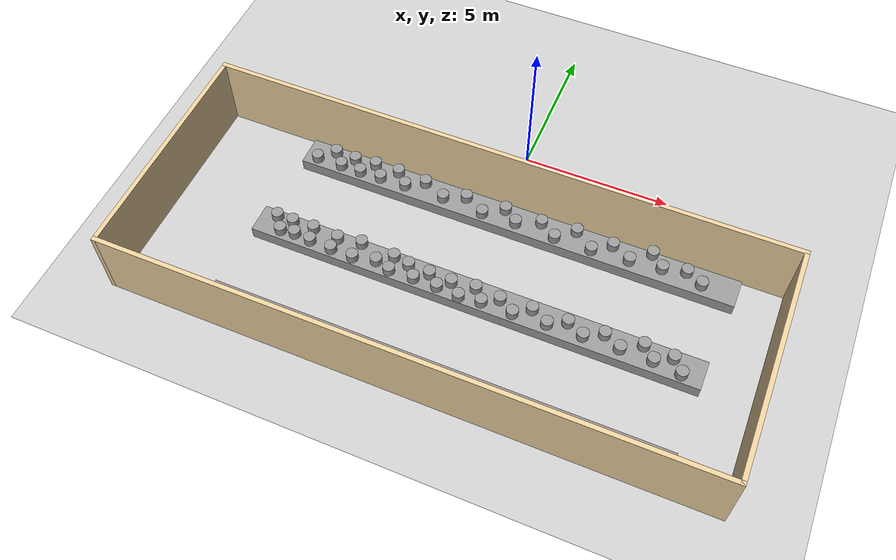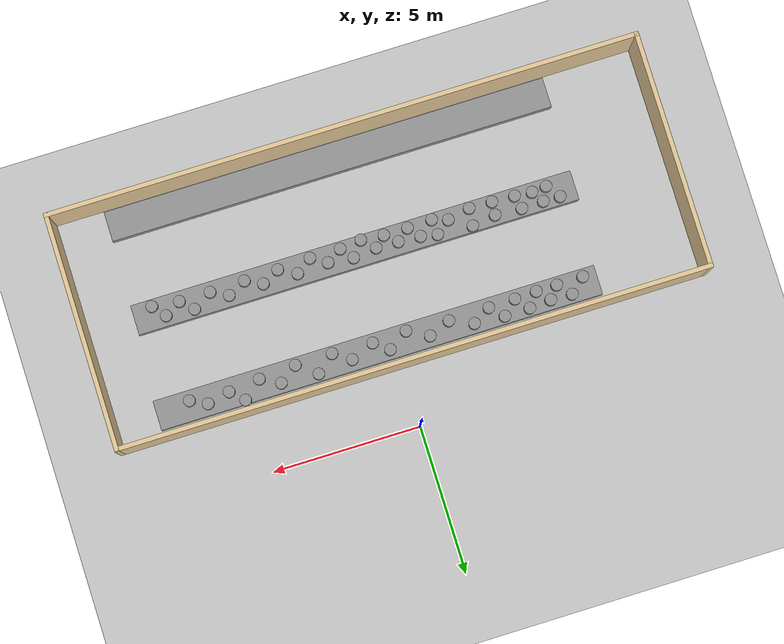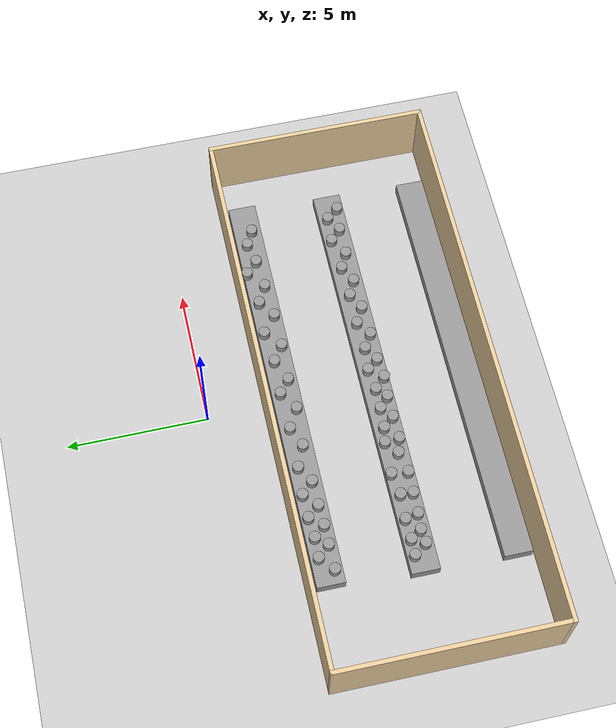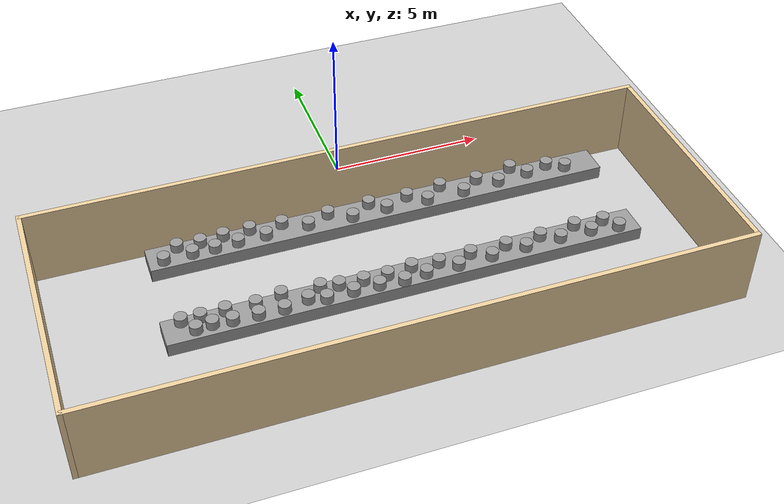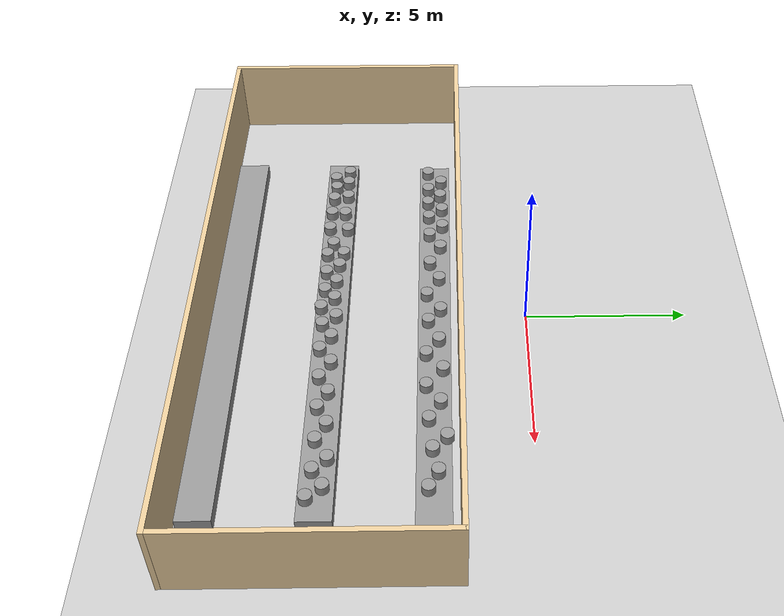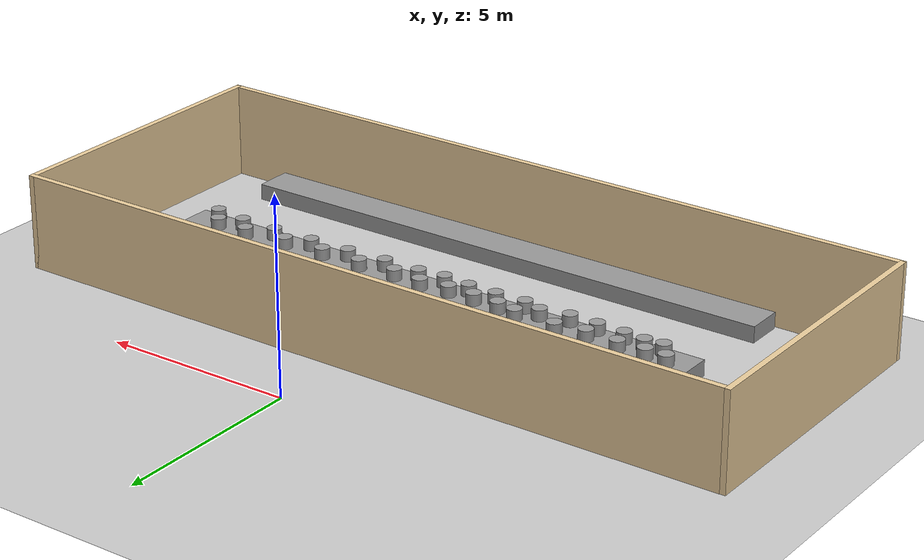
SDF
<sdf version="1.7">
 <world name="default">
  <light name="sun" type="directional">
   <pose>0 0 10 0 -0 0</pose>
   <diffuse>0.8 0.8 0.8 1</diffuse>
   <specular>0.2 0.2 0.2 1</specular>
   <attenuation>
    <range>1000</range>
    <constant>0.9</constant>
    <linear>0.01</linear>
    <quadratic>0.001</quadratic>
   </attenuation>
   <direction>-0.5 0.1 -0.9</direction>
   <spot><inner_angle>0</inner_angle><outer_angle>0</outer_angle><falloff>0</falloff></spot>
  </light>
  <model name="ground_plane">
   <static>1</static>
   <link name="link">
    <collision name="collision">
     <geometry><plane><normal>0 0 1</normal><size>100 100</size></plane></geometry>
     <surface>
      <contact><collide_bitmask>65535</collide_bitmask></contact>
      <friction><ode><mu>100</mu><mu2>50</mu2></ode></friction>
     </surface>
    </collision>
    <visual name="visual">
     <cast_shadows>0</cast_shadows>
     <geometry><plane><normal>0 0 1</normal><size>100 100</size></plane></geometry>
     <material>
      <script><uri>file://media/materials/scripts/gazebo.material</uri><name>Gazebo/Grey</name></script>
     </material>
    </visual>
   </link>
  </model>
  <gravity>0 0 -9.8</gravity>
  <magnetic_field>6e-06 2.3e-05 -4.2e-05</magnetic_field>
  <atmosphere type="adiabatic"/>
  <physics type="ode">
   <max_step_size>0.001</max_step_size>
   <real_time_factor>1</real_time_factor>
   <real_time_update_rate>1000</real_time_update_rate>
  </physics>
  <scene><ambient>0.4 0.4 0.4 1</ambient><background>0.7 0.7 0.7 1</background><shadows>1</shadows></scene>
  <spherical_coordinates>
   <surface_model>EARTH_WGS84</surface_model>
   <latitude_deg>0</latitude_deg>
   <longitude_deg>0</longitude_deg>
   <elevation>0</elevation>
   <heading_deg>0</heading_deg>
  </spherical_coordinates>
  <model name="Test_Building">
   <pose>-0.420117 -4.99407 0 0 -0 0</pose>
   <link name="Wall_3">
    <collision name="Wall_3_Collision">
     <geometry><box><size>20 0.15 2.5</size></box></geometry>
     <pose>0 0 1.25 0 -0 0</pose>
    </collision>
    <visual name="Wall_3_Visual">
     <pose>0 0 1.25 0 -0 0</pose>
     <geometry><box><size>20 0.15 2.5</size></box></geometry>
     <material>
      <script><uri>file://media/materials/scripts/gazebo.material</uri><name>Gazebo/Grey</name></script>
      <ambient>0.921569 0.807843 0.615686 1</ambient>
     </material>
     <meta><layer>0</layer></meta>
    </visual>
    <pose>0 2.93093 0 0 -0 0</pose>
   </link>
   <link name="Wall_4">
    <collision name="Wall_4_Collision">
     <geometry><box><size>8 0.15 2.5</size></box></geometry>
     <pose>0 0 1.25 0 -0 0</pose>
    </collision>
    <visual name="Wall_4_Visual">
     <pose>0 0 1.25 0 -0 0</pose>
     <geometry><box><size>8 0.15 2.5</size></box></geometry>
     <material>
      <script><uri>file://media/materials/scripts/gazebo.material</uri><name>Gazebo/Grey</name></script>
      <ambient>0.921569 0.807843 0.615686 1</ambient>
     </material>
     <meta><layer>0</layer></meta>
    </visual>
    <pose>9.925 -0.994068 0 0 -0 -1.5708</pose>
   </link>
   <link name="Wall_5">
    <collision name="Wall_5_Collision">
     <geometry><box><size>20 0.15 2.5</size></box></geometry>
     <pose>0 0 1.25 0 -0 0</pose>
    </collision>
    <visual name="Wall_5_Visual">
     <pose>0 0 1.25 0 -0 0</pose>
     <geometry><box><size>20 0.15 2.5</size></box></geometry>
     <material>
      <script><uri>file://media/materials/scripts/gazebo.material</uri><name>Gazebo/Grey</name></script>
      <ambient>0.921569 0.807843 0.615686 1</ambient>
     </material>
     <meta><layer>0</layer></meta>
    </visual>
    <pose>0 -4.91907 0 0 -0 3.14159</pose>
   </link>
   <link name="Wall_6">
    <collision name="Wall_6_Collision">
     <geometry><box><size>8 0.15 2.5</size></box></geometry>
     <pose>0 0 1.25 0 -0 0</pose>
    </collision>
    <visual name="Wall_6_Visual">
     <pose>0 0 1.25 0 -0 0</pose>
     <geometry><box><size>8 0.15 2.5</size></box></geometry>
     <material>
      <script><uri>file://media/materials/scripts/gazebo.material</uri><name>Gazebo/Grey</name></script>
      <ambient>0.921569 0.807843 0.615686 1</ambient>
     </material>
     <meta><layer>0</layer></meta>
    </visual>
    <pose>-9.925 -0.994068 0 0 -0 1.5708</pose>
   </link>
   <static>1</static>
  </model>
  <model name="Test_Bench">
   <link name="link_1">
    <inertial>
     <mass>6.47546</mass>
     <inertia><ixx>0.639529</ixx><ixy>0</ixy><ixz>0</ixz><iyy>122.309</iyy><iyz>0</iyz><izz>122.749</izz></inertia>
    </inertial>
    <pose>-0 4e-06 0 0 -0 0</pose>
    <visual name="visual">
     <geometry><box><size>15.049 1 0.430283</size></box></geometry>
     <material>
      <lighting>1</lighting>
      <script><uri>file://media/materials/scripts/gazebo.material</uri><name>Gazebo/Grey</name></script>
      <shader type="pixel"/>
     </material>
    </visual>
    <collision name="collision">
     <geometry><box><size>15.049 1 0.430283</size></box></geometry>
     <surface>
      <friction>
       <ode><mu>1</mu><mu2>1</mu2><fdir1>0 0 0</fdir1><slip1>0</slip1><slip2>0</slip2></ode>
       <torsional>
        <coefficient>1</coefficient>
        <patch_radius>0</patch_radius>
        <surface_radius>0</surface_radius>
        <use_patch_radius>1</use_patch_radius>
        <ode><slip>0</slip></ode>
       </torsional>
      </friction>
      <bounce><restitution_coefficient>0</restitution_coefficient><threshold>1e+06</threshold></bounce>
      <contact>
       <collide_without_contact>0</collide_without_contact>
       <collide_without_contact_bitmask>1</collide_without_contact_bitmask>
       <collide_bitmask>1</collide_bitmask>
       <ode>
        <soft_cfm>0</soft_cfm>
        <soft_erp>0.2</soft_erp>
        <kp>1e+13</kp>
        <kd>1</kd>
        <max_vel>0.01</max_vel>
        <min_depth>0</min_depth>
       </ode>
       <bullet>
        <split_impulse>1</split_impulse>
        <split_impulse_penetration_threshold>-0.01</split_impulse_penetration_threshold>
        <soft_cfm>0</soft_cfm>
        <soft_erp>0.2</soft_erp>
        <kp>1e+13</kp>
        <kd>1</kd>
       </bullet>
      </contact>
     </surface>
    </collision>
   </link>
   <static>0</static>
   <pose>0.548934 -2.85968 0.215134 -1.4e-05 -0 9e-06</pose>
  </model>
  <model name="Test_Bench_clone">
   <link name="link_1">
    <inertial>
     <mass>6.47546</mass>
     <inertia><ixx>0.639529</ixx><ixy>0</ixy><ixz>0</ixz><iyy>122.309</iyy><iyz>0</iyz><izz>122.749</izz></inertia>
    </inertial>
    <pose>-0 4e-06 0 0 -0 0</pose>
    <visual name="visual">
     <geometry><box><size>15.049 1 0.430283</size></box></geometry>
     <material>
      <lighting>1</lighting>
      <script><uri>file://media/materials/scripts/gazebo.material</uri><name>Gazebo/Grey</name></script>
      <shader type="pixel"/>
     </material>
    </visual>
    <collision name="collision">
     <geometry><box><size>15.049 1 0.430283</size></box></geometry>
     <surface>
      <friction>
       <ode><mu>1</mu><mu2>1</mu2><fdir1>0 0 0</fdir1><slip1>0</slip1><slip2>0</slip2></ode>
       <torsional>
        <coefficient>1</coefficient>
        <patch_radius>0</patch_radius>
        <surface_radius>0</surface_radius>
        <use_patch_radius>1</use_patch_radius>
        <ode><slip>0</slip></ode>
       </torsional>
      </friction>
      <bounce><restitution_coefficient>0</restitution_coefficient><threshold>1e+06</threshold></bounce>
      <contact>
       <collide_without_contact>0</collide_without_contact>
       <collide_without_contact_bitmask>1</collide_without_contact_bitmask>
       <collide_bitmask>1</collide_bitmask>
       <ode>
        <soft_cfm>0</soft_cfm>
        <soft_erp>0.2</soft_erp>
        <kp>1e+13</kp>
        <kd>1</kd>
        <max_vel>0.01</max_vel>
        <min_depth>0</min_depth>
       </ode>
       <bullet>
        <split_impulse>1</split_impulse>
        <split_impulse_penetration_threshold>-0.01</split_impulse_penetration_threshold>
        <soft_cfm>0</soft_cfm>
        <soft_erp>0.2</soft_erp>
        <kp>1e+13</kp>
        <kd>1</kd>
       </bullet>
      </contact>
     </surface>
    </collision>
   </link>
   <static>0</static>
   <pose>0.345714 -6.05819 0.215135 -1.4e-05 -0 2e-06</pose>
  </model>
  <model name="Test_Bench_clone_0">
   <link name="link_1">
    <inertial>
     <mass>6.47546</mass>
     <inertia><ixx>0.639529</ixx><ixy>0</ixy><ixz>0</ixz><iyy>122.309</iyy><iyz>0</iyz><izz>122.749</izz></inertia>
    </inertial>
    <pose>-0 4e-06 0 0 -0 0</pose>
    <visual name="visual">
     <geometry><box><size>15.049 1 0.430283</size></box></geometry>
     <material>
      <lighting>1</lighting>
      <script><uri>file://media/materials/scripts/gazebo.material</uri><name>Gazebo/Grey</name></script>
      <shader type="pixel"/>
     </material>
    </visual>
    <collision name="collision">
     <geometry><box><size>15.049 1 0.430283</size></box></geometry>
     <surface>
      <friction>
       <ode><mu>1</mu><mu2>1</mu2><fdir1>0 0 0</fdir1><slip1>0</slip1><slip2>0</slip2></ode>
       <torsional>
        <coefficient>1</coefficient>
        <patch_radius>0</patch_radius>
        <surface_radius>0</surface_radius>
        <use_patch_radius>1</use_patch_radius>
        <ode><slip>0</slip></ode>
       </torsional>
      </friction>
      <bounce><restitution_coefficient>0</restitution_coefficient><threshold>1e+06</threshold></bounce>
      <contact>
       <collide_without_contact>0</collide_without_contact>
       <collide_without_contact_bitmask>1</collide_without_contact_bitmask>
       <collide_bitmask>1</collide_bitmask>
       <ode>
        <soft_cfm>0</soft_cfm>
        <soft_erp>0.2</soft_erp>
        <kp>1e+13</kp>
        <kd>1</kd>
        <max_vel>0.01</max_vel>
        <min_depth>0</min_depth>
       </ode>
       <bullet>
        <split_impulse>1</split_impulse>
        <split_impulse_penetration_threshold>-0.01</split_impulse_penetration_threshold>
        <soft_cfm>0</soft_cfm>
        <soft_erp>0.2</soft_erp>
        <kp>1e+13</kp>
        <kd>1</kd>
       </bullet>
      </contact>
     </surface>
    </collision>
   </link>
   <static>0</static>
   <pose>0.286602 -9.2541 0.215141 0 -0 0</pose>
  </model>
  <model name="Test_pot">
   <link name="link_0">
    <inertial>
     <mass>0.044841</mass>
     <inertia>
      <ixx>0.000748065</ixx>
      <ixy>0</ixy>
      <ixz>0</ixz>
      <iyy>0.000748065</iyy>
      <iyz>0</iyz>
      <izz>0.000864954</izz>
     </inertia>
    </inertial>
    <pose>3e-06 1e-06 0 0 -0 0</pose>
    <visual name="visual">
     <geometry><cylinder><radius>0.196415</radius><length>0.290612</length></cylinder></geometry>
     <material>
      <lighting>1</lighting>
      <script><uri>file://media/materials/scripts/gazebo.material</uri><name>Gazebo/Grey</name></script>
      <shader type="pixel"/>
     </material>
    </visual>
    <collision name="collision">
     <geometry><cylinder><radius>0.196415</radius><length>0.290612</length></cylinder></geometry>
     <surface>
      <friction>
       <ode><mu>1</mu><mu2>1</mu2><fdir1>0 0 0</fdir1><slip1>0</slip1><slip2>0</slip2></ode>
       <torsional>
        <coefficient>1</coefficient>
        <patch_radius>0</patch_radius>
        <surface_radius>0</surface_radius>
        <use_patch_radius>1</use_patch_radius>
        <ode><slip>0</slip></ode>
       </torsional>
      </friction>
      <bounce><restitution_coefficient>0</restitution_coefficient><threshold>1e+06</threshold></bounce>
      <contact>
       <collide_without_contact>0</collide_without_contact>
       <collide_without_contact_bitmask>1</collide_without_contact_bitmask>
       <collide_bitmask>1</collide_bitmask>
       <ode>
        <soft_cfm>0</soft_cfm>
        <soft_erp>0.2</soft_erp>
        <kp>1e+13</kp>
        <kd>1</kd>
        <max_vel>0.01</max_vel>
        <min_depth>0</min_depth>
       </ode>
       <bullet>
        <split_impulse>1</split_impulse>
        <split_impulse_penetration_threshold>-0.01</split_impulse_penetration_threshold>
        <soft_cfm>0</soft_cfm>
        <soft_erp>0.2</soft_erp>
        <kp>1e+13</kp>
        <kd>1</kd>
       </bullet>
      </contact>
     </surface>
    </collision>
   </link>
   <static>0</static>
   <pose>-6.50438 -3.08268 0.575595 -2.2e-05 -1e-05 -0.000529</pose>
  </model>
  <model name="Test_pot_clone">
   <link name="link_0">
    <inertial>
     <mass>0.044841</mass>
     <inertia>
      <ixx>0.000748065</ixx>
      <ixy>0</ixy>
      <ixz>0</ixz>
      <iyy>0.000748065</iyy>
      <iyz>0</iyz>
      <izz>0.000864954</izz>
     </inertia>
    </inertial>
    <pose>3e-06 1e-06 0 0 -0 0</pose>
    <visual name="visual">
     <geometry><cylinder><radius>0.196415</radius><length>0.290612</length></cylinder></geometry>
     <material>
      <lighting>1</lighting>
      <script><uri>file://media/materials/scripts/gazebo.material</uri><name>Gazebo/Grey</name></script>
      <shader type="pixel"/>
     </material>
    </visual>
    <collision name="collision">
     <geometry><cylinder><radius>0.196415</radius><length>0.290612</length></cylinder></geometry>
     <surface>
      <friction>
       <ode><mu>1</mu><mu2>1</mu2><fdir1>0 0 0</fdir1><slip1>0</slip1><slip2>0</slip2></ode>
       <torsional>
        <coefficient>1</coefficient>
        <patch_radius>0</patch_radius>
        <surface_radius>0</surface_radius>
        <use_patch_radius>1</use_patch_radius>
        <ode><slip>0</slip></ode>
       </torsional>
      </friction>
      <bounce><restitution_coefficient>0</restitution_coefficient><threshold>1e+06</threshold></bounce>
      <contact>
       <collide_without_contact>0</collide_without_contact>
       <collide_without_contact_bitmask>1</collide_without_contact_bitmask>
       <collide_bitmask>1</collide_bitmask>
       <ode>
        <soft_cfm>0</soft_cfm>
        <soft_erp>0.2</soft_erp>
        <kp>1e+13</kp>
        <kd>1</kd>
        <max_vel>0.01</max_vel>
        <min_depth>0</min_depth>
       </ode>
       <bullet>
        <split_impulse>1</split_impulse>
        <split_impulse_penetration_threshold>-0.01</split_impulse_penetration_threshold>
        <soft_cfm>0</soft_cfm>
        <soft_erp>0.2</soft_erp>
        <kp>1e+13</kp>
        <kd>1</kd>
       </bullet>
      </contact>
     </surface>
    </collision>
   </link>
   <static>0</static>
   <pose>-6.00654 -2.63855 0.57558 2e-06 3e-06 -0.000579</pose>
  </model>
  <model name="Test_pot_clone_0">
   <link name="link_0">
    <inertial>
     <mass>0.044841</mass>
     <inertia>
      <ixx>0.000748065</ixx>
      <ixy>0</ixy>
      <ixz>0</ixz>
      <iyy>0.000748065</iyy>
      <iyz>0</iyz>
      <izz>0.000864954</izz>
     </inertia>
    </inertial>
    <pose>3e-06 1e-06 0 0 -0 0</pose>
    <visual name="visual">
     <geometry><cylinder><radius>0.196415</radius><length>0.290612</length></cylinder></geometry>
     <material>
      <lighting>1</lighting>
      <script><uri>file://media/materials/scripts/gazebo.material</uri><name>Gazebo/Grey</name></script>
      <shader type="pixel"/>
     </material>
    </visual>
    <collision name="collision">
     <geometry><cylinder><radius>0.196415</radius><length>0.290612</length></cylinder></geometry>
     <surface>
      <friction>
       <ode><mu>1</mu><mu2>1</mu2><fdir1>0 0 0</fdir1><slip1>0</slip1><slip2>0</slip2></ode>
       <torsional>
        <coefficient>1</coefficient>
        <patch_radius>0</patch_radius>
        <surface_radius>0</surface_radius>
        <use_patch_radius>1</use_patch_radius>
        <ode><slip>0</slip></ode>
       </torsional>
      </friction>
      <bounce><restitution_coefficient>0</restitution_coefficient><threshold>1e+06</threshold></bounce>
      <contact>
       <collide_without_contact>0</collide_without_contact>
       <collide_without_contact_bitmask>1</collide_without_contact_bitmask>
       <collide_bitmask>1</collide_bitmask>
       <ode>
        <soft_cfm>0</soft_cfm>
        <soft_erp>0.2</soft_erp>
        <kp>1e+13</kp>
        <kd>1</kd>
        <max_vel>0.01</max_vel>
        <min_depth>0</min_depth>
       </ode>
       <bullet>
        <split_impulse>1</split_impulse>
        <split_impulse_penetration_threshold>-0.01</split_impulse_penetration_threshold>
        <soft_cfm>0</soft_cfm>
        <soft_erp>0.2</soft_erp>
        <kp>1e+13</kp>
        <kd>1</kd>
       </bullet>
      </contact>
     </surface>
    </collision>
   </link>
   <static>0</static>
   <pose>-5.61248 -3.07277 0.575587 -1e-06 -3e-06 -0.000655</pose>
  </model>
  <model name="Test_pot_clone_1">
   <link name="link_0">
    <inertial>
     <mass>0.044841</mass>
     <inertia>
      <ixx>0.000748065</ixx>
      <ixy>0</ixy>
      <ixz>0</ixz>
      <iyy>0.000748065</iyy>
      <iyz>0</iyz>
      <izz>0.000864954</izz>
     </inertia>
    </inertial>
    <pose>3e-06 1e-06 0 0 -0 0</pose>
    <visual name="visual">
     <geometry><cylinder><radius>0.196415</radius><length>0.290612</length></cylinder></geometry>
     <material>
      <lighting>1</lighting>
      <script><uri>file://media/materials/scripts/gazebo.material</uri><name>Gazebo/Grey</name></script>
      <shader type="pixel"/>
     </material>
    </visual>
    <collision name="collision">
     <geometry><cylinder><radius>0.196415</radius><length>0.290612</length></cylinder></geometry>
     <surface>
      <friction>
       <ode><mu>1</mu><mu2>1</mu2><fdir1>0 0 0</fdir1><slip1>0</slip1><slip2>0</slip2></ode>
       <torsional>
        <coefficient>1</coefficient>
        <patch_radius>0</patch_radius>
        <surface_radius>0</surface_radius>
        <use_patch_radius>1</use_patch_radius>
        <ode><slip>0</slip></ode>
       </torsional>
      </friction>
      <bounce><restitution_coefficient>0</restitution_coefficient><threshold>1e+06</threshold></bounce>
      <contact>
       <collide_without_contact>0</collide_without_contact>
       <collide_without_contact_bitmask>1</collide_without_contact_bitmask>
       <collide_bitmask>1</collide_bitmask>
       <ode>
        <soft_cfm>0</soft_cfm>
        <soft_erp>0.2</soft_erp>
        <kp>1e+13</kp>
        <kd>1</kd>
        <max_vel>0.01</max_vel>
        <min_depth>0</min_depth>
       </ode>
       <bullet>
        <split_impulse>1</split_impulse>
        <split_impulse_penetration_threshold>-0.01</split_impulse_penetration_threshold>
        <soft_cfm>0</soft_cfm>
        <soft_erp>0.2</soft_erp>
        <kp>1e+13</kp>
        <kd>1</kd>
       </bullet>
      </contact>
     </surface>
    </collision>
   </link>
   <static>0</static>
   <pose>-5.28132 -2.67032 0.575583 -1.8e-05 -0 -0.000617</pose>
  </model>
  <model name="Test_pot_clone_2">
   <link name="link_0">
    <inertial>
     <mass>0.044841</mass>
     <inertia>
      <ixx>0.000748065</ixx>
      <ixy>0</ixy>
      <ixz>0</ixz>
      <iyy>0.000748065</iyy>
      <iyz>0</iyz>
      <izz>0.000864954</izz>
     </inertia>
    </inertial>
    <pose>3e-06 1e-06 0 0 -0 0</pose>
    <visual name="visual">
     <geometry><cylinder><radius>0.196415</radius><length>0.290612</length></cylinder></geometry>
     <material>
      <lighting>1</lighting>
      <script><uri>file://media/materials/scripts/gazebo.material</uri><name>Gazebo/Grey</name></script>
      <shader type="pixel"/>
     </material>
    </visual>
    <collision name="collision">
     <geometry><cylinder><radius>0.196415</radius><length>0.290612</length></cylinder></geometry>
     <surface>
      <friction>
       <ode><mu>1</mu><mu2>1</mu2><fdir1>0 0 0</fdir1><slip1>0</slip1><slip2>0</slip2></ode>
       <torsional>
        <coefficient>1</coefficient>
        <patch_radius>0</patch_radius>
        <surface_radius>0</surface_radius>
        <use_patch_radius>1</use_patch_radius>
        <ode><slip>0</slip></ode>
       </torsional>
      </friction>
      <bounce><restitution_coefficient>0</restitution_coefficient><threshold>1e+06</threshold></bounce>
      <contact>
       <collide_without_contact>0</collide_without_contact>
       <collide_without_contact_bitmask>1</collide_without_contact_bitmask>
       <collide_bitmask>1</collide_bitmask>
       <ode>
        <soft_cfm>0</soft_cfm>
        <soft_erp>0.2</soft_erp>
        <kp>1e+13</kp>
        <kd>1</kd>
        <max_vel>0.01</max_vel>
        <min_depth>0</min_depth>
       </ode>
       <bullet>
        <split_impulse>1</split_impulse>
        <split_impulse_penetration_threshold>-0.01</split_impulse_penetration_threshold>
        <soft_cfm>0</soft_cfm>
        <soft_erp>0.2</soft_erp>
        <kp>1e+13</kp>
        <kd>1</kd>
       </bullet>
      </contact>
     </surface>
    </collision>
   </link>
   <static>0</static>
   <pose>-4.90848 -3.07316 0.575591 1.6e-05 -1.3e-05 -0.000533</pose>
  </model>
  <model name="Test_pot_clone_3">
   <link name="link_0">
    <inertial>
     <mass>0.044841</mass>
     <inertia>
      <ixx>0.000748065</ixx>
      <ixy>0</ixy>
      <ixz>0</ixz>
      <iyy>0.000748065</iyy>
      <iyz>0</iyz>
      <izz>0.000864954</izz>
     </inertia>
    </inertial>
    <pose>3e-06 1e-06 0 0 -0 0</pose>
    <visual name="visual">
     <geometry><cylinder><radius>0.196415</radius><length>0.290612</length></cylinder></geometry>
     <material>
      <lighting>1</lighting>
      <script><uri>file://media/materials/scripts/gazebo.material</uri><name>Gazebo/Grey</name></script>
      <shader type="pixel"/>
     </material>
    </visual>
    <collision name="collision">
     <geometry><cylinder><radius>0.196415</radius><length>0.290612</length></cylinder></geometry>
     <surface>
      <friction>
       <ode><mu>1</mu><mu2>1</mu2><fdir1>0 0 0</fdir1><slip1>0</slip1><slip2>0</slip2></ode>
       <torsional>
        <coefficient>1</coefficient>
        <patch_radius>0</patch_radius>
        <surface_radius>0</surface_radius>
        <use_patch_radius>1</use_patch_radius>
        <ode><slip>0</slip></ode>
       </torsional>
      </friction>
      <bounce><restitution_coefficient>0</restitution_coefficient><threshold>1e+06</threshold></bounce>
      <contact>
       <collide_without_contact>0</collide_without_contact>
       <collide_without_contact_bitmask>1</collide_without_contact_bitmask>
       <collide_bitmask>1</collide_bitmask>
       <ode>
        <soft_cfm>0</soft_cfm>
        <soft_erp>0.2</soft_erp>
        <kp>1e+13</kp>
        <kd>1</kd>
        <max_vel>0.01</max_vel>
        <min_depth>0</min_depth>
       </ode>
       <bullet>
        <split_impulse>1</split_impulse>
        <split_impulse_penetration_threshold>-0.01</split_impulse_penetration_threshold>
        <soft_cfm>0</soft_cfm>
        <soft_erp>0.2</soft_erp>
        <kp>1e+13</kp>
        <kd>1</kd>
       </bullet>
      </contact>
     </surface>
    </collision>
   </link>
   <static>0</static>
   <pose>-4.54601 -2.61106 0.57558 -4e-06 -4e-06 -0.000541</pose>
  </model>
  <model name="Test_pot_clone_4">
   <link name="link_0">
    <inertial>
     <mass>0.044841</mass>
     <inertia>
      <ixx>0.000748065</ixx>
      <ixy>0</ixy>
      <ixz>0</ixz>
      <iyy>0.000748065</iyy>
      <iyz>0</iyz>
      <izz>0.000864954</izz>
     </inertia>
    </inertial>
    <pose>3e-06 1e-06 0 0 -0 0</pose>
    <visual name="visual">
     <geometry><cylinder><radius>0.196415</radius><length>0.290612</length></cylinder></geometry>
     <material>
      <lighting>1</lighting>
      <script><uri>file://media/materials/scripts/gazebo.material</uri><name>Gazebo/Grey</name></script>
      <shader type="pixel"/>
     </material>
    </visual>
    <collision name="collision">
     <geometry><cylinder><radius>0.196415</radius><length>0.290612</length></cylinder></geometry>
     <surface>
      <friction>
       <ode><mu>1</mu><mu2>1</mu2><fdir1>0 0 0</fdir1><slip1>0</slip1><slip2>0</slip2></ode>
       <torsional>
        <coefficient>1</coefficient>
        <patch_radius>0</patch_radius>
        <surface_radius>0</surface_radius>
        <use_patch_radius>1</use_patch_radius>
        <ode><slip>0</slip></ode>
       </torsional>
      </friction>
      <bounce><restitution_coefficient>0</restitution_coefficient><threshold>1e+06</threshold></bounce>
      <contact>
       <collide_without_contact>0</collide_without_contact>
       <collide_without_contact_bitmask>1</collide_without_contact_bitmask>
       <collide_bitmask>1</collide_bitmask>
       <ode>
        <soft_cfm>0</soft_cfm>
        <soft_erp>0.2</soft_erp>
        <kp>1e+13</kp>
        <kd>1</kd>
        <max_vel>0.01</max_vel>
        <min_depth>0</min_depth>
       </ode>
       <bullet>
        <split_impulse>1</split_impulse>
        <split_impulse_penetration_threshold>-0.01</split_impulse_penetration_threshold>
        <soft_cfm>0</soft_cfm>
        <soft_erp>0.2</soft_erp>
        <kp>1e+13</kp>
        <kd>1</kd>
       </bullet>
      </contact>
     </surface>
    </collision>
   </link>
   <static>0</static>
   <pose>-4.17136 -3.04137 0.575587 -4e-06 8e-06 -0.000548</pose>
  </model>
  <model name="Test_pot_clone_5">
   <link name="link_0">
    <inertial>
     <mass>0.044841</mass>
     <inertia>
      <ixx>0.000748065</ixx>
      <ixy>0</ixy>
      <ixz>0</ixz>
      <iyy>0.000748065</iyy>
      <iyz>0</iyz>
      <izz>0.000864954</izz>
     </inertia>
    </inertial>
    <pose>3e-06 1e-06 0 0 -0 0</pose>
    <visual name="visual">
     <geometry><cylinder><radius>0.196415</radius><length>0.290612</length></cylinder></geometry>
     <material>
      <lighting>1</lighting>
      <script><uri>file://media/materials/scripts/gazebo.material</uri><name>Gazebo/Grey</name></script>
      <shader type="pixel"/>
     </material>
    </visual>
    <collision name="collision">
     <geometry><cylinder><radius>0.196415</radius><length>0.290612</length></cylinder></geometry>
     <surface>
      <friction>
       <ode><mu>1</mu><mu2>1</mu2><fdir1>0 0 0</fdir1><slip1>0</slip1><slip2>0</slip2></ode>
       <torsional>
        <coefficient>1</coefficient>
        <patch_radius>0</patch_radius>
        <surface_radius>0</surface_radius>
        <use_patch_radius>1</use_patch_radius>
        <ode><slip>0</slip></ode>
       </torsional>
      </friction>
      <bounce><restitution_coefficient>0</restitution_coefficient><threshold>1e+06</threshold></bounce>
      <contact>
       <collide_without_contact>0</collide_without_contact>
       <collide_without_contact_bitmask>1</collide_without_contact_bitmask>
       <collide_bitmask>1</collide_bitmask>
       <ode>
        <soft_cfm>0</soft_cfm>
        <soft_erp>0.2</soft_erp>
        <kp>1e+13</kp>
        <kd>1</kd>
        <max_vel>0.01</max_vel>
        <min_depth>0</min_depth>
       </ode>
       <bullet>
        <split_impulse>1</split_impulse>
        <split_impulse_penetration_threshold>-0.01</split_impulse_penetration_threshold>
        <soft_cfm>0</soft_cfm>
        <soft_erp>0.2</soft_erp>
        <kp>1e+13</kp>
        <kd>1</kd>
       </bullet>
      </contact>
     </surface>
    </collision>
   </link>
   <static>0</static>
   <pose>-3.6948 -2.59942 0.575584 1.5e-05 7e-06 -0.000418</pose>
  </model>
  <model name="Test_pot_clone_6">
   <link name="link_0">
    <inertial>
     <mass>0.044841</mass>
     <inertia>
      <ixx>0.000748065</ixx>
      <ixy>0</ixy>
      <ixz>0</ixz>
      <iyy>0.000748065</iyy>
      <iyz>0</iyz>
      <izz>0.000864954</izz>
     </inertia>
    </inertial>
    <pose>3e-06 1e-06 0 0 -0 0</pose>
    <visual name="visual">
     <geometry><cylinder><radius>0.196415</radius><length>0.290612</length></cylinder></geometry>
     <material>
      <lighting>1</lighting>
      <script><uri>file://media/materials/scripts/gazebo.material</uri><name>Gazebo/Grey</name></script>
      <shader type="pixel"/>
     </material>
    </visual>
    <collision name="collision">
     <geometry><cylinder><radius>0.196415</radius><length>0.290612</length></cylinder></geometry>
     <surface>
      <friction>
       <ode><mu>1</mu><mu2>1</mu2><fdir1>0 0 0</fdir1><slip1>0</slip1><slip2>0</slip2></ode>
       <torsional>
        <coefficient>1</coefficient>
        <patch_radius>0</patch_radius>
        <surface_radius>0</surface_radius>
        <use_patch_radius>1</use_patch_radius>
        <ode><slip>0</slip></ode>
       </torsional>
      </friction>
      <bounce><restitution_coefficient>0</restitution_coefficient><threshold>1e+06</threshold></bounce>
      <contact>
       <collide_without_contact>0</collide_without_contact>
       <collide_without_contact_bitmask>1</collide_without_contact_bitmask>
       <collide_bitmask>1</collide_bitmask>
       <ode>
        <soft_cfm>0</soft_cfm>
        <soft_erp>0.2</soft_erp>
        <kp>1e+13</kp>
        <kd>1</kd>
        <max_vel>0.01</max_vel>
        <min_depth>0</min_depth>
       </ode>
       <bullet>
        <split_impulse>1</split_impulse>
        <split_impulse_penetration_threshold>-0.01</split_impulse_penetration_threshold>
        <soft_cfm>0</soft_cfm>
        <soft_erp>0.2</soft_erp>
        <kp>1e+13</kp>
        <kd>1</kd>
       </bullet>
      </contact>
     </surface>
    </collision>
   </link>
   <static>0</static>
   <pose>-3.27506 -3.02162 0.57559 1e-05 -1e-06 -0.000254</pose>
  </model>
  <model name="Test_pot_clone_7">
   <link name="link_0">
    <inertial>
     <mass>0.044841</mass>
     <inertia>
      <ixx>0.000748065</ixx>
      <ixy>0</ixy>
      <ixz>0</ixz>
      <iyy>0.000748065</iyy>
      <iyz>0</iyz>
      <izz>0.000864954</izz>
     </inertia>
    </inertial>
    <pose>3e-06 1e-06 0 0 -0 0</pose>
    <visual name="visual">
     <geometry><cylinder><radius>0.196415</radius><length>0.290612</length></cylinder></geometry>
     <material>
      <lighting>1</lighting>
      <script><uri>file://media/materials/scripts/gazebo.material</uri><name>Gazebo/Grey</name></script>
      <shader type="pixel"/>
     </material>
    </visual>
    <collision name="collision">
     <geometry><cylinder><radius>0.196415</radius><length>0.290612</length></cylinder></geometry>
     <surface>
      <friction>
       <ode><mu>1</mu><mu2>1</mu2><fdir1>0 0 0</fdir1><slip1>0</slip1><slip2>0</slip2></ode>
       <torsional>
        <coefficient>1</coefficient>
        <patch_radius>0</patch_radius>
        <surface_radius>0</surface_radius>
        <use_patch_radius>1</use_patch_radius>
        <ode><slip>0</slip></ode>
       </torsional>
      </friction>
      <bounce><restitution_coefficient>0</restitution_coefficient><threshold>1e+06</threshold></bounce>
      <contact>
       <collide_without_contact>0</collide_without_contact>
       <collide_without_contact_bitmask>1</collide_without_contact_bitmask>
       <collide_bitmask>1</collide_bitmask>
       <ode>
        <soft_cfm>0</soft_cfm>
        <soft_erp>0.2</soft_erp>
        <kp>1e+13</kp>
        <kd>1</kd>
        <max_vel>0.01</max_vel>
        <min_depth>0</min_depth>
       </ode>
       <bullet>
        <split_impulse>1</split_impulse>
        <split_impulse_penetration_threshold>-0.01</split_impulse_penetration_threshold>
        <soft_cfm>0</soft_cfm>
        <soft_erp>0.2</soft_erp>
        <kp>1e+13</kp>
        <kd>1</kd>
       </bullet>
      </contact>
     </surface>
    </collision>
   </link>
   <static>0</static>
   <pose>-2.67651 -2.66455 0.575579 -1.4e-05 2e-06 -0.000386</pose>
  </model>
  <model name="Test_pot_clone_8">
   <link name="link_0">
    <inertial>
     <mass>0.044841</mass>
     <inertia>
      <ixx>0.000748065</ixx>
      <ixy>0</ixy>
      <ixz>0</ixz>
      <iyy>0.000748065</iyy>
      <iyz>0</iyz>
      <izz>0.000864954</izz>
     </inertia>
    </inertial>
    <pose>3e-06 1e-06 0 0 -0 0</pose>
    <visual name="visual">
     <geometry><cylinder><radius>0.196415</radius><length>0.290612</length></cylinder></geometry>
     <material>
      <lighting>1</lighting>
      <script><uri>file://media/materials/scripts/gazebo.material</uri><name>Gazebo/Grey</name></script>
      <shader type="pixel"/>
     </material>
    </visual>
    <collision name="collision">
     <geometry><cylinder><radius>0.196415</radius><length>0.290612</length></cylinder></geometry>
     <surface>
      <friction>
       <ode><mu>1</mu><mu2>1</mu2><fdir1>0 0 0</fdir1><slip1>0</slip1><slip2>0</slip2></ode>
       <torsional>
        <coefficient>1</coefficient>
        <patch_radius>0</patch_radius>
        <surface_radius>0</surface_radius>
        <use_patch_radius>1</use_patch_radius>
        <ode><slip>0</slip></ode>
       </torsional>
      </friction>
      <bounce><restitution_coefficient>0</restitution_coefficient><threshold>1e+06</threshold></bounce>
      <contact>
       <collide_without_contact>0</collide_without_contact>
       <collide_without_contact_bitmask>1</collide_without_contact_bitmask>
       <collide_bitmask>1</collide_bitmask>
       <ode>
        <soft_cfm>0</soft_cfm>
        <soft_erp>0.2</soft_erp>
        <kp>1e+13</kp>
        <kd>1</kd>
        <max_vel>0.01</max_vel>
        <min_depth>0</min_depth>
       </ode>
       <bullet>
        <split_impulse>1</split_impulse>
        <split_impulse_penetration_threshold>-0.01</split_impulse_penetration_threshold>
        <soft_cfm>0</soft_cfm>
        <soft_erp>0.2</soft_erp>
        <kp>1e+13</kp>
        <kd>1</kd>
       </bullet>
      </contact>
     </surface>
    </collision>
   </link>
   <static>0</static>
   <pose>-1.90554 -2.99928 0.575587 -3e-05 1e-05 -0.000545</pose>
  </model>
  <model name="Test_pot_clone_9">
   <link name="link_0">
    <inertial>
     <mass>0.044841</mass>
     <inertia>
      <ixx>0.000748065</ixx>
      <ixy>0</ixy>
      <ixz>0</ixz>
      <iyy>0.000748065</iyy>
      <iyz>0</iyz>
      <izz>0.000864954</izz>
     </inertia>
    </inertial>
    <pose>3e-06 1e-06 0 0 -0 0</pose>
    <visual name="visual">
     <geometry><cylinder><radius>0.196415</radius><length>0.290612</length></cylinder></geometry>
     <material>
      <lighting>1</lighting>
      <script><uri>file://media/materials/scripts/gazebo.material</uri><name>Gazebo/Grey</name></script>
      <shader type="pixel"/>
     </material>
    </visual>
    <collision name="collision">
     <geometry><cylinder><radius>0.196415</radius><length>0.290612</length></cylinder></geometry>
     <surface>
      <friction>
       <ode><mu>1</mu><mu2>1</mu2><fdir1>0 0 0</fdir1><slip1>0</slip1><slip2>0</slip2></ode>
       <torsional>
        <coefficient>1</coefficient>
        <patch_radius>0</patch_radius>
        <surface_radius>0</surface_radius>
        <use_patch_radius>1</use_patch_radius>
        <ode><slip>0</slip></ode>
       </torsional>
      </friction>
      <bounce><restitution_coefficient>0</restitution_coefficient><threshold>1e+06</threshold></bounce>
      <contact>
       <collide_without_contact>0</collide_without_contact>
       <collide_without_contact_bitmask>1</collide_without_contact_bitmask>
       <collide_bitmask>1</collide_bitmask>
       <ode>
        <soft_cfm>0</soft_cfm>
        <soft_erp>0.2</soft_erp>
        <kp>1e+13</kp>
        <kd>1</kd>
        <max_vel>0.01</max_vel>
        <min_depth>0</min_depth>
       </ode>
       <bullet>
        <split_impulse>1</split_impulse>
        <split_impulse_penetration_threshold>-0.01</split_impulse_penetration_threshold>
        <soft_cfm>0</soft_cfm>
        <soft_erp>0.2</soft_erp>
        <kp>1e+13</kp>
        <kd>1</kd>
       </bullet>
      </contact>
     </surface>
    </collision>
   </link>
   <static>0</static>
   <pose>-1.17974 -2.7047 0.575608 -5.6e-05 -6e-06 -0.000283</pose>
  </model>
  <model name="Test_pot_clone_10">
   <link name="link_0">
    <inertial>
     <mass>0.044841</mass>
     <inertia>
      <ixx>0.000748065</ixx>
      <ixy>0</ixy>
      <ixz>0</ixz>
      <iyy>0.000748065</iyy>
      <iyz>0</iyz>
      <izz>0.000864954</izz>
     </inertia>
    </inertial>
    <pose>3e-06 1e-06 0 0 -0 0</pose>
    <visual name="visual">
     <geometry><cylinder><radius>0.196415</radius><length>0.290612</length></cylinder></geometry>
     <material>
      <lighting>1</lighting>
      <script><uri>file://media/materials/scripts/gazebo.material</uri><name>Gazebo/Grey</name></script>
      <shader type="pixel"/>
     </material>
    </visual>
    <collision name="collision">
     <geometry><cylinder><radius>0.196415</radius><length>0.290612</length></cylinder></geometry>
     <surface>
      <friction>
       <ode><mu>1</mu><mu2>1</mu2><fdir1>0 0 0</fdir1><slip1>0</slip1><slip2>0</slip2></ode>
       <torsional>
        <coefficient>1</coefficient>
        <patch_radius>0</patch_radius>
        <surface_radius>0</surface_radius>
        <use_patch_radius>1</use_patch_radius>
        <ode><slip>0</slip></ode>
       </torsional>
      </friction>
      <bounce><restitution_coefficient>0</restitution_coefficient><threshold>1e+06</threshold></bounce>
      <contact>
       <collide_without_contact>0</collide_without_contact>
       <collide_without_contact_bitmask>1</collide_without_contact_bitmask>
       <collide_bitmask>1</collide_bitmask>
       <ode>
        <soft_cfm>0</soft_cfm>
        <soft_erp>0.2</soft_erp>
        <kp>1e+13</kp>
        <kd>1</kd>
        <max_vel>0.01</max_vel>
        <min_depth>0</min_depth>
       </ode>
       <bullet>
        <split_impulse>1</split_impulse>
        <split_impulse_penetration_threshold>-0.01</split_impulse_penetration_threshold>
        <soft_cfm>0</soft_cfm>
        <soft_erp>0.2</soft_erp>
        <kp>1e+13</kp>
        <kd>1</kd>
       </bullet>
      </contact>
     </surface>
    </collision>
   </link>
   <static>0</static>
   <pose>-0.473543 -3.09195 0.575592 1.9e-05 1.1e-05 -0.000312</pose>
  </model>
  <model name="Test_pot_clone_11">
   <link name="link_0">
    <inertial>
     <mass>0.044841</mass>
     <inertia>
      <ixx>0.000748065</ixx>
      <ixy>0</ixy>
      <ixz>0</ixz>
      <iyy>0.000748065</iyy>
      <iyz>0</iyz>
      <izz>0.000864954</izz>
     </inertia>
    </inertial>
    <pose>3e-06 1e-06 0 0 -0 0</pose>
    <visual name="visual">
     <geometry><cylinder><radius>0.196415</radius><length>0.290612</length></cylinder></geometry>
     <material>
      <lighting>1</lighting>
      <script><uri>file://media/materials/scripts/gazebo.material</uri><name>Gazebo/Grey</name></script>
      <shader type="pixel"/>
     </material>
    </visual>
    <collision name="collision">
     <geometry><cylinder><radius>0.196415</radius><length>0.290612</length></cylinder></geometry>
     <surface>
      <friction>
       <ode><mu>1</mu><mu2>1</mu2><fdir1>0 0 0</fdir1><slip1>0</slip1><slip2>0</slip2></ode>
       <torsional>
        <coefficient>1</coefficient>
        <patch_radius>0</patch_radius>
        <surface_radius>0</surface_radius>
        <use_patch_radius>1</use_patch_radius>
        <ode><slip>0</slip></ode>
       </torsional>
      </friction>
      <bounce><restitution_coefficient>0</restitution_coefficient><threshold>1e+06</threshold></bounce>
      <contact>
       <collide_without_contact>0</collide_without_contact>
       <collide_without_contact_bitmask>1</collide_without_contact_bitmask>
       <collide_bitmask>1</collide_bitmask>
       <ode>
        <soft_cfm>0</soft_cfm>
        <soft_erp>0.2</soft_erp>
        <kp>1e+13</kp>
        <kd>1</kd>
        <max_vel>0.01</max_vel>
        <min_depth>0</min_depth>
       </ode>
       <bullet>
        <split_impulse>1</split_impulse>
        <split_impulse_penetration_threshold>-0.01</split_impulse_penetration_threshold>
        <soft_cfm>0</soft_cfm>
        <soft_erp>0.2</soft_erp>
        <kp>1e+13</kp>
        <kd>1</kd>
       </bullet>
      </contact>
     </surface>
    </collision>
   </link>
   <static>0</static>
   <pose>0.194224 -2.66129 0.575591 -5.6e-05 -3e-06 -0.000585</pose>
  </model>
  <model name="Test_pot_clone_12">
   <link name="link_0">
    <inertial>
     <mass>0.044841</mass>
     <inertia>
      <ixx>0.000748065</ixx>
      <ixy>0</ixy>
      <ixz>0</ixz>
      <iyy>0.000748065</iyy>
      <iyz>0</iyz>
      <izz>0.000864954</izz>
     </inertia>
    </inertial>
    <pose>3e-06 1e-06 0 0 -0 0</pose>
    <visual name="visual">
     <geometry><cylinder><radius>0.196415</radius><length>0.290612</length></cylinder></geometry>
     <material>
      <lighting>1</lighting>
      <script><uri>file://media/materials/scripts/gazebo.material</uri><name>Gazebo/Grey</name></script>
      <shader type="pixel"/>
     </material>
    </visual>
    <collision name="collision">
     <geometry><cylinder><radius>0.196415</radius><length>0.290612</length></cylinder></geometry>
     <surface>
      <friction>
       <ode><mu>1</mu><mu2>1</mu2><fdir1>0 0 0</fdir1><slip1>0</slip1><slip2>0</slip2></ode>
       <torsional>
        <coefficient>1</coefficient>
        <patch_radius>0</patch_radius>
        <surface_radius>0</surface_radius>
        <use_patch_radius>1</use_patch_radius>
        <ode><slip>0</slip></ode>
       </torsional>
      </friction>
      <bounce><restitution_coefficient>0</restitution_coefficient><threshold>1e+06</threshold></bounce>
      <contact>
       <collide_without_contact>0</collide_without_contact>
       <collide_without_contact_bitmask>1</collide_without_contact_bitmask>
       <collide_bitmask>1</collide_bitmask>
       <ode>
        <soft_cfm>0</soft_cfm>
        <soft_erp>0.2</soft_erp>
        <kp>1e+13</kp>
        <kd>1</kd>
        <max_vel>0.01</max_vel>
        <min_depth>0</min_depth>
       </ode>
       <bullet>
        <split_impulse>1</split_impulse>
        <split_impulse_penetration_threshold>-0.01</split_impulse_penetration_threshold>
        <soft_cfm>0</soft_cfm>
        <soft_erp>0.2</soft_erp>
        <kp>1e+13</kp>
        <kd>1</kd>
       </bullet>
      </contact>
     </surface>
    </collision>
   </link>
   <static>0</static>
   <pose>0.679639 -3.0407 0.575586 -5e-06 -4e-06 -0.000507</pose>
  </model>
  <model name="Test_pot_clone_13">
   <link name="link_0">
    <inertial>
     <mass>0.044841</mass>
     <inertia>
      <ixx>0.000748065</ixx>
      <ixy>0</ixy>
      <ixz>0</ixz>
      <iyy>0.000748065</iyy>
      <iyz>0</iyz>
      <izz>0.000864954</izz>
     </inertia>
    </inertial>
    <pose>3e-06 1e-06 0 0 -0 0</pose>
    <visual name="visual">
     <geometry><cylinder><radius>0.196415</radius><length>0.290612</length></cylinder></geometry>
     <material>
      <lighting>1</lighting>
      <script><uri>file://media/materials/scripts/gazebo.material</uri><name>Gazebo/Grey</name></script>
      <shader type="pixel"/>
     </material>
    </visual>
    <collision name="collision">
     <geometry><cylinder><radius>0.196415</radius><length>0.290612</length></cylinder></geometry>
     <surface>
      <friction>
       <ode><mu>1</mu><mu2>1</mu2><fdir1>0 0 0</fdir1><slip1>0</slip1><slip2>0</slip2></ode>
       <torsional>
        <coefficient>1</coefficient>
        <patch_radius>0</patch_radius>
        <surface_radius>0</surface_radius>
        <use_patch_radius>1</use_patch_radius>
        <ode><slip>0</slip></ode>
       </torsional>
      </friction>
      <bounce><restitution_coefficient>0</restitution_coefficient><threshold>1e+06</threshold></bounce>
      <contact>
       <collide_without_contact>0</collide_without_contact>
       <collide_without_contact_bitmask>1</collide_without_contact_bitmask>
       <collide_bitmask>1</collide_bitmask>
       <ode>
        <soft_cfm>0</soft_cfm>
        <soft_erp>0.2</soft_erp>
        <kp>1e+13</kp>
        <kd>1</kd>
        <max_vel>0.01</max_vel>
        <min_depth>0</min_depth>
       </ode>
       <bullet>
        <split_impulse>1</split_impulse>
        <split_impulse_penetration_threshold>-0.01</split_impulse_penetration_threshold>
        <soft_cfm>0</soft_cfm>
        <soft_erp>0.2</soft_erp>
        <kp>1e+13</kp>
        <kd>1</kd>
       </bullet>
      </contact>
     </surface>
    </collision>
   </link>
   <static>0</static>
   <pose>1.47064 -2.71563 0.575582 -2.5e-05 1e-06 -0.00057</pose>
  </model>
  <model name="Test_pot_clone_14">
   <link name="link_0">
    <inertial>
     <mass>0.044841</mass>
     <inertia>
      <ixx>0.000748065</ixx>
      <ixy>0</ixy>
      <ixz>0</ixz>
      <iyy>0.000748065</iyy>
      <iyz>0</iyz>
      <izz>0.000864954</izz>
     </inertia>
    </inertial>
    <pose>3e-06 1e-06 0 0 -0 0</pose>
    <visual name="visual">
     <geometry><cylinder><radius>0.196415</radius><length>0.290612</length></cylinder></geometry>
     <material>
      <lighting>1</lighting>
      <script><uri>file://media/materials/scripts/gazebo.material</uri><name>Gazebo/Grey</name></script>
      <shader type="pixel"/>
     </material>
    </visual>
    <collision name="collision">
     <geometry><cylinder><radius>0.196415</radius><length>0.290612</length></cylinder></geometry>
     <surface>
      <friction>
       <ode><mu>1</mu><mu2>1</mu2><fdir1>0 0 0</fdir1><slip1>0</slip1><slip2>0</slip2></ode>
       <torsional>
        <coefficient>1</coefficient>
        <patch_radius>0</patch_radius>
        <surface_radius>0</surface_radius>
        <use_patch_radius>1</use_patch_radius>
        <ode><slip>0</slip></ode>
       </torsional>
      </friction>
      <bounce><restitution_coefficient>0</restitution_coefficient><threshold>1e+06</threshold></bounce>
      <contact>
       <collide_without_contact>0</collide_without_contact>
       <collide_without_contact_bitmask>1</collide_without_contact_bitmask>
       <collide_bitmask>1</collide_bitmask>
       <ode>
        <soft_cfm>0</soft_cfm>
        <soft_erp>0.2</soft_erp>
        <kp>1e+13</kp>
        <kd>1</kd>
        <max_vel>0.01</max_vel>
        <min_depth>0</min_depth>
       </ode>
       <bullet>
        <split_impulse>1</split_impulse>
        <split_impulse_penetration_threshold>-0.01</split_impulse_penetration_threshold>
        <soft_cfm>0</soft_cfm>
        <soft_erp>0.2</soft_erp>
        <kp>1e+13</kp>
        <kd>1</kd>
       </bullet>
      </contact>
     </surface>
    </collision>
   </link>
   <static>0</static>
   <pose>2.04477 -3.09911 0.575586 -1.3e-05 -2e-06 -0.000704</pose>
  </model>
  <model name="Test_pot_clone_15">
   <link name="link_0">
    <inertial>
     <mass>0.044841</mass>
     <inertia>
      <ixx>0.000748065</ixx>
      <ixy>0</ixy>
      <ixz>0</ixz>
      <iyy>0.000748065</iyy>
      <iyz>0</iyz>
      <izz>0.000864954</izz>
     </inertia>
    </inertial>
    <pose>3e-06 1e-06 0 0 -0 0</pose>
    <visual name="visual">
     <geometry><cylinder><radius>0.196415</radius><length>0.290612</length></cylinder></geometry>
     <material>
      <lighting>1</lighting>
      <script><uri>file://media/materials/scripts/gazebo.material</uri><name>Gazebo/Grey</name></script>
      <shader type="pixel"/>
     </material>
    </visual>
    <collision name="collision">
     <geometry><cylinder><radius>0.196415</radius><length>0.290612</length></cylinder></geometry>
     <surface>
      <friction>
       <ode><mu>1</mu><mu2>1</mu2><fdir1>0 0 0</fdir1><slip1>0</slip1><slip2>0</slip2></ode>
       <torsional>
        <coefficient>1</coefficient>
        <patch_radius>0</patch_radius>
        <surface_radius>0</surface_radius>
        <use_patch_radius>1</use_patch_radius>
        <ode><slip>0</slip></ode>
       </torsional>
      </friction>
      <bounce><restitution_coefficient>0</restitution_coefficient><threshold>1e+06</threshold></bounce>
      <contact>
       <collide_without_contact>0</collide_without_contact>
       <collide_without_contact_bitmask>1</collide_without_contact_bitmask>
       <collide_bitmask>1</collide_bitmask>
       <ode>
        <soft_cfm>0</soft_cfm>
        <soft_erp>0.2</soft_erp>
        <kp>1e+13</kp>
        <kd>1</kd>
        <max_vel>0.01</max_vel>
        <min_depth>0</min_depth>
       </ode>
       <bullet>
        <split_impulse>1</split_impulse>
        <split_impulse_penetration_threshold>-0.01</split_impulse_penetration_threshold>
        <soft_cfm>0</soft_cfm>
        <soft_erp>0.2</soft_erp>
        <kp>1e+13</kp>
        <kd>1</kd>
       </bullet>
      </contact>
     </surface>
    </collision>
   </link>
   <static>0</static>
   <pose>2.64881 -2.59643 0.57558 -2.3e-05 1e-06 -0.000498</pose>
  </model>
  <model name="Test_pot_clone_16">
   <link name="link_0">
    <inertial>
     <mass>0.044841</mass>
     <inertia>
      <ixx>0.000748065</ixx>
      <ixy>0</ixy>
      <ixz>0</ixz>
      <iyy>0.000748065</iyy>
      <iyz>0</iyz>
      <izz>0.000864954</izz>
     </inertia>
    </inertial>
    <pose>3e-06 1e-06 0 0 -0 0</pose>
    <visual name="visual">
     <geometry><cylinder><radius>0.196415</radius><length>0.290612</length></cylinder></geometry>
     <material>
      <lighting>1</lighting>
      <script><uri>file://media/materials/scripts/gazebo.material</uri><name>Gazebo/Grey</name></script>
      <shader type="pixel"/>
     </material>
    </visual>
    <collision name="collision">
     <geometry><cylinder><radius>0.196415</radius><length>0.290612</length></cylinder></geometry>
     <surface>
      <friction>
       <ode><mu>1</mu><mu2>1</mu2><fdir1>0 0 0</fdir1><slip1>0</slip1><slip2>0</slip2></ode>
       <torsional>
        <coefficient>1</coefficient>
        <patch_radius>0</patch_radius>
        <surface_radius>0</surface_radius>
        <use_patch_radius>1</use_patch_radius>
        <ode><slip>0</slip></ode>
       </torsional>
      </friction>
      <bounce><restitution_coefficient>0</restitution_coefficient><threshold>1e+06</threshold></bounce>
      <contact>
       <collide_without_contact>0</collide_without_contact>
       <collide_without_contact_bitmask>1</collide_without_contact_bitmask>
       <collide_bitmask>1</collide_bitmask>
       <ode>
        <soft_cfm>0</soft_cfm>
        <soft_erp>0.2</soft_erp>
        <kp>1e+13</kp>
        <kd>1</kd>
        <max_vel>0.01</max_vel>
        <min_depth>0</min_depth>
       </ode>
       <bullet>
        <split_impulse>1</split_impulse>
        <split_impulse_penetration_threshold>-0.01</split_impulse_penetration_threshold>
        <soft_cfm>0</soft_cfm>
        <soft_erp>0.2</soft_erp>
        <kp>1e+13</kp>
        <kd>1</kd>
       </bullet>
      </contact>
     </surface>
    </collision>
   </link>
   <static>0</static>
   <pose>3.29426 -3.09315 0.57559 8e-06 9e-06 -0.000687</pose>
  </model>
  <model name="Test_pot_clone_17">
   <link name="link_0">
    <inertial>
     <mass>0.044841</mass>
     <inertia>
      <ixx>0.000748065</ixx>
      <ixy>0</ixy>
      <ixz>0</ixz>
      <iyy>0.000748065</iyy>
      <iyz>0</iyz>
      <izz>0.000864954</izz>
     </inertia>
    </inertial>
    <pose>3e-06 1e-06 0 0 -0 0</pose>
    <visual name="visual">
     <geometry><cylinder><radius>0.196415</radius><length>0.290612</length></cylinder></geometry>
     <material>
      <lighting>1</lighting>
      <script><uri>file://media/materials/scripts/gazebo.material</uri><name>Gazebo/Grey</name></script>
      <shader type="pixel"/>
     </material>
    </visual>
    <collision name="collision">
     <geometry><cylinder><radius>0.196415</radius><length>0.290612</length></cylinder></geometry>
     <surface>
      <friction>
       <ode><mu>1</mu><mu2>1</mu2><fdir1>0 0 0</fdir1><slip1>0</slip1><slip2>0</slip2></ode>
       <torsional>
        <coefficient>1</coefficient>
        <patch_radius>0</patch_radius>
        <surface_radius>0</surface_radius>
        <use_patch_radius>1</use_patch_radius>
        <ode><slip>0</slip></ode>
       </torsional>
      </friction>
      <bounce><restitution_coefficient>0</restitution_coefficient><threshold>1e+06</threshold></bounce>
      <contact>
       <collide_without_contact>0</collide_without_contact>
       <collide_without_contact_bitmask>1</collide_without_contact_bitmask>
       <collide_bitmask>1</collide_bitmask>
       <ode>
        <soft_cfm>0</soft_cfm>
        <soft_erp>0.2</soft_erp>
        <kp>1e+13</kp>
        <kd>1</kd>
        <max_vel>0.01</max_vel>
        <min_depth>0</min_depth>
       </ode>
       <bullet>
        <split_impulse>1</split_impulse>
        <split_impulse_penetration_threshold>-0.01</split_impulse_penetration_threshold>
        <soft_cfm>0</soft_cfm>
        <soft_erp>0.2</soft_erp>
        <kp>1e+13</kp>
        <kd>1</kd>
       </bullet>
      </contact>
     </surface>
    </collision>
   </link>
   <static>0</static>
   <pose>3.89865 -2.66951 0.57558 -1.7e-05 -0 -0.000385</pose>
  </model>
  <model name="Test_pot_clone_18">
   <link name="link_0">
    <inertial>
     <mass>0.044841</mass>
     <inertia>
      <ixx>0.000748065</ixx>
      <ixy>0</ixy>
      <ixz>0</ixz>
      <iyy>0.000748065</iyy>
      <iyz>0</iyz>
      <izz>0.000864954</izz>
     </inertia>
    </inertial>
    <pose>3e-06 1e-06 0 0 -0 0</pose>
    <visual name="visual">
     <geometry><cylinder><radius>0.196415</radius><length>0.290612</length></cylinder></geometry>
     <material>
      <lighting>1</lighting>
      <script><uri>file://media/materials/scripts/gazebo.material</uri><name>Gazebo/Grey</name></script>
      <shader type="pixel"/>
     </material>
    </visual>
    <collision name="collision">
     <geometry><cylinder><radius>0.196415</radius><length>0.290612</length></cylinder></geometry>
     <surface>
      <friction>
       <ode><mu>1</mu><mu2>1</mu2><fdir1>0 0 0</fdir1><slip1>0</slip1><slip2>0</slip2></ode>
       <torsional>
        <coefficient>1</coefficient>
        <patch_radius>0</patch_radius>
        <surface_radius>0</surface_radius>
        <use_patch_radius>1</use_patch_radius>
        <ode><slip>0</slip></ode>
       </torsional>
      </friction>
      <bounce><restitution_coefficient>0</restitution_coefficient><threshold>1e+06</threshold></bounce>
      <contact>
       <collide_without_contact>0</collide_without_contact>
       <collide_without_contact_bitmask>1</collide_without_contact_bitmask>
       <collide_bitmask>1</collide_bitmask>
       <ode>
        <soft_cfm>0</soft_cfm>
        <soft_erp>0.2</soft_erp>
        <kp>1e+13</kp>
        <kd>1</kd>
        <max_vel>0.01</max_vel>
        <min_depth>0</min_depth>
       </ode>
       <bullet>
        <split_impulse>1</split_impulse>
        <split_impulse_penetration_threshold>-0.01</split_impulse_penetration_threshold>
        <soft_cfm>0</soft_cfm>
        <soft_erp>0.2</soft_erp>
        <kp>1e+13</kp>
        <kd>1</kd>
       </bullet>
      </contact>
     </surface>
    </collision>
   </link>
   <static>0</static>
   <pose>4.54505 -3.00659 0.575594 3.9e-05 -2e-06 -0.0003</pose>
  </model>
  <model name="Test_pot_clone_19">
   <link name="link_0">
    <inertial>
     <mass>0.044841</mass>
     <inertia>
      <ixx>0.000748065</ixx>
      <ixy>0</ixy>
      <ixz>0</ixz>
      <iyy>0.000748065</iyy>
      <iyz>0</iyz>
      <izz>0.000864954</izz>
     </inertia>
    </inertial>
    <pose>3e-06 1e-06 0 0 -0 0</pose>
    <visual name="visual">
     <geometry><cylinder><radius>0.196415</radius><length>0.290612</length></cylinder></geometry>
     <material>
      <lighting>1</lighting>
      <script><uri>file://media/materials/scripts/gazebo.material</uri><name>Gazebo/Grey</name></script>
      <shader type="pixel"/>
     </material>
    </visual>
    <collision name="collision">
     <geometry><cylinder><radius>0.196415</radius><length>0.290612</length></cylinder></geometry>
     <surface>
      <friction>
       <ode><mu>1</mu><mu2>1</mu2><fdir1>0 0 0</fdir1><slip1>0</slip1><slip2>0</slip2></ode>
       <torsional>
        <coefficient>1</coefficient>
        <patch_radius>0</patch_radius>
        <surface_radius>0</surface_radius>
        <use_patch_radius>1</use_patch_radius>
        <ode><slip>0</slip></ode>
       </torsional>
      </friction>
      <bounce><restitution_coefficient>0</restitution_coefficient><threshold>1e+06</threshold></bounce>
      <contact>
       <collide_without_contact>0</collide_without_contact>
       <collide_without_contact_bitmask>1</collide_without_contact_bitmask>
       <collide_bitmask>1</collide_bitmask>
       <ode>
        <soft_cfm>0</soft_cfm>
        <soft_erp>0.2</soft_erp>
        <kp>1e+13</kp>
        <kd>1</kd>
        <max_vel>0.01</max_vel>
        <min_depth>0</min_depth>
       </ode>
       <bullet>
        <split_impulse>1</split_impulse>
        <split_impulse_penetration_threshold>-0.01</split_impulse_penetration_threshold>
        <soft_cfm>0</soft_cfm>
        <soft_erp>0.2</soft_erp>
        <kp>1e+13</kp>
        <kd>1</kd>
       </bullet>
      </contact>
     </surface>
    </collision>
   </link>
   <static>0</static>
   <pose>5.16829 -2.48542 0.575587 -5e-06 5.3e-05 -0.000472</pose>
  </model>
  <model name="Test_pot_clone_20">
   <link name="link_0">
    <inertial>
     <mass>0.044841</mass>
     <inertia>
      <ixx>0.000748065</ixx>
      <ixy>0</ixy>
      <ixz>0</ixz>
      <iyy>0.000748065</iyy>
      <iyz>0</iyz>
      <izz>0.000864954</izz>
     </inertia>
    </inertial>
    <pose>3e-06 1e-06 0 0 -0 0</pose>
    <visual name="visual">
     <geometry><cylinder><radius>0.196415</radius><length>0.290612</length></cylinder></geometry>
     <material>
      <lighting>1</lighting>
      <script><uri>file://media/materials/scripts/gazebo.material</uri><name>Gazebo/Grey</name></script>
      <shader type="pixel"/>
     </material>
    </visual>
    <collision name="collision">
     <geometry><cylinder><radius>0.196415</radius><length>0.290612</length></cylinder></geometry>
     <surface>
      <friction>
       <ode><mu>1</mu><mu2>1</mu2><fdir1>0 0 0</fdir1><slip1>0</slip1><slip2>0</slip2></ode>
       <torsional>
        <coefficient>1</coefficient>
        <patch_radius>0</patch_radius>
        <surface_radius>0</surface_radius>
        <use_patch_radius>1</use_patch_radius>
        <ode><slip>0</slip></ode>
       </torsional>
      </friction>
      <bounce><restitution_coefficient>0</restitution_coefficient><threshold>1e+06</threshold></bounce>
      <contact>
       <collide_without_contact>0</collide_without_contact>
       <collide_without_contact_bitmask>1</collide_without_contact_bitmask>
       <collide_bitmask>1</collide_bitmask>
       <ode>
        <soft_cfm>0</soft_cfm>
        <soft_erp>0.2</soft_erp>
        <kp>1e+13</kp>
        <kd>1</kd>
        <max_vel>0.01</max_vel>
        <min_depth>0</min_depth>
       </ode>
       <bullet>
        <split_impulse>1</split_impulse>
        <split_impulse_penetration_threshold>-0.01</split_impulse_penetration_threshold>
        <soft_cfm>0</soft_cfm>
        <soft_erp>0.2</soft_erp>
        <kp>1e+13</kp>
        <kd>1</kd>
       </bullet>
      </contact>
     </surface>
    </collision>
   </link>
   <static>0</static>
   <pose>5.60424 -2.90045 0.575586 -2.7e-05 1.4e-05 -0.000422</pose>
  </model>
  <model name="Test_pot_clone_21">
   <link name="link_0">
    <inertial>
     <mass>0.044841</mass>
     <inertia>
      <ixx>0.000748065</ixx>
      <ixy>0</ixy>
      <ixz>0</ixz>
      <iyy>0.000748065</iyy>
      <iyz>0</iyz>
      <izz>0.000864954</izz>
     </inertia>
    </inertial>
    <pose>3e-06 1e-06 0 0 -0 0</pose>
    <visual name="visual">
     <geometry><cylinder><radius>0.196415</radius><length>0.290612</length></cylinder></geometry>
     <material>
      <lighting>1</lighting>
      <script><uri>file://media/materials/scripts/gazebo.material</uri><name>Gazebo/Grey</name></script>
      <shader type="pixel"/>
     </material>
    </visual>
    <collision name="collision">
     <geometry><cylinder><radius>0.196415</radius><length>0.290612</length></cylinder></geometry>
     <surface>
      <friction>
       <ode><mu>1</mu><mu2>1</mu2><fdir1>0 0 0</fdir1><slip1>0</slip1><slip2>0</slip2></ode>
       <torsional>
        <coefficient>1</coefficient>
        <patch_radius>0</patch_radius>
        <surface_radius>0</surface_radius>
        <use_patch_radius>1</use_patch_radius>
        <ode><slip>0</slip></ode>
       </torsional>
      </friction>
      <bounce><restitution_coefficient>0</restitution_coefficient><threshold>1e+06</threshold></bounce>
      <contact>
       <collide_without_contact>0</collide_without_contact>
       <collide_without_contact_bitmask>1</collide_without_contact_bitmask>
       <collide_bitmask>1</collide_bitmask>
       <ode>
        <soft_cfm>0</soft_cfm>
        <soft_erp>0.2</soft_erp>
        <kp>1e+13</kp>
        <kd>1</kd>
        <max_vel>0.01</max_vel>
        <min_depth>0</min_depth>
       </ode>
       <bullet>
        <split_impulse>1</split_impulse>
        <split_impulse_penetration_threshold>-0.01</split_impulse_penetration_threshold>
        <soft_cfm>0</soft_cfm>
        <soft_erp>0.2</soft_erp>
        <kp>1e+13</kp>
        <kd>1</kd>
       </bullet>
      </contact>
     </surface>
    </collision>
   </link>
   <static>0</static>
   <pose>6.36774 -2.73338 0.57558 -1.4e-05 0 -0.000467</pose>
  </model>
  <model name="Test_pot_clone_22">
   <link name="link_0">
    <inertial>
     <mass>0.044841</mass>
     <inertia>
      <ixx>0.000748065</ixx>
      <ixy>0</ixy>
      <ixz>0</ixz>
      <iyy>0.000748065</iyy>
      <iyz>0</iyz>
      <izz>0.000864954</izz>
     </inertia>
    </inertial>
    <pose>3e-06 1e-06 0 0 -0 0</pose>
    <visual name="visual">
     <geometry><cylinder><radius>0.196415</radius><length>0.290612</length></cylinder></geometry>
     <material>
      <lighting>1</lighting>
      <script><uri>file://media/materials/scripts/gazebo.material</uri><name>Gazebo/Grey</name></script>
      <shader type="pixel"/>
     </material>
    </visual>
    <collision name="collision">
     <geometry><cylinder><radius>0.196415</radius><length>0.290612</length></cylinder></geometry>
     <surface>
      <friction>
       <ode><mu>1</mu><mu2>1</mu2><fdir1>0 0 0</fdir1><slip1>0</slip1><slip2>0</slip2></ode>
       <torsional>
        <coefficient>1</coefficient>
        <patch_radius>0</patch_radius>
        <surface_radius>0</surface_radius>
        <use_patch_radius>1</use_patch_radius>
        <ode><slip>0</slip></ode>
       </torsional>
      </friction>
      <bounce><restitution_coefficient>0</restitution_coefficient><threshold>1e+06</threshold></bounce>
      <contact>
       <collide_without_contact>0</collide_without_contact>
       <collide_without_contact_bitmask>1</collide_without_contact_bitmask>
       <collide_bitmask>1</collide_bitmask>
       <ode>
        <soft_cfm>0</soft_cfm>
        <soft_erp>0.2</soft_erp>
        <kp>1e+13</kp>
        <kd>1</kd>
        <max_vel>0.01</max_vel>
        <min_depth>0</min_depth>
       </ode>
       <bullet>
        <split_impulse>1</split_impulse>
        <split_impulse_penetration_threshold>-0.01</split_impulse_penetration_threshold>
        <soft_cfm>0</soft_cfm>
        <soft_erp>0.2</soft_erp>
        <kp>1e+13</kp>
        <kd>1</kd>
       </bullet>
      </contact>
     </surface>
    </collision>
   </link>
   <static>0</static>
   <pose>6.91835 -3.0068 0.575592 -3.5e-05 3.8e-05 -0.000504</pose>
  </model>
  <model name="Test_pot_clone_23">
   <link name="link_0">
    <inertial>
     <mass>0.044841</mass>
     <inertia>
      <ixx>0.000748065</ixx>
      <ixy>0</ixy>
      <ixz>0</ixz>
      <iyy>0.000748065</iyy>
      <iyz>0</iyz>
      <izz>0.000864954</izz>
     </inertia>
    </inertial>
    <pose>3e-06 1e-06 0 0 -0 0</pose>
    <visual name="visual">
     <geometry><cylinder><radius>0.196415</radius><length>0.290612</length></cylinder></geometry>
     <material>
      <lighting>1</lighting>
      <script><uri>file://media/materials/scripts/gazebo.material</uri><name>Gazebo/Grey</name></script>
      <shader type="pixel"/>
     </material>
    </visual>
    <collision name="collision">
     <geometry><cylinder><radius>0.196415</radius><length>0.290612</length></cylinder></geometry>
     <surface>
      <friction>
       <ode><mu>1</mu><mu2>1</mu2><fdir1>0 0 0</fdir1><slip1>0</slip1><slip2>0</slip2></ode>
       <torsional>
        <coefficient>1</coefficient>
        <patch_radius>0</patch_radius>
        <surface_radius>0</surface_radius>
        <use_patch_radius>1</use_patch_radius>
        <ode><slip>0</slip></ode>
       </torsional>
      </friction>
      <bounce><restitution_coefficient>0</restitution_coefficient><threshold>1e+06</threshold></bounce>
      <contact>
       <collide_without_contact>0</collide_without_contact>
       <collide_without_contact_bitmask>1</collide_without_contact_bitmask>
       <collide_bitmask>1</collide_bitmask>
       <ode>
        <soft_cfm>0</soft_cfm>
        <soft_erp>0.2</soft_erp>
        <kp>1e+13</kp>
        <kd>1</kd>
        <max_vel>0.01</max_vel>
        <min_depth>0</min_depth>
       </ode>
       <bullet>
        <split_impulse>1</split_impulse>
        <split_impulse_penetration_threshold>-0.01</split_impulse_penetration_threshold>
        <soft_cfm>0</soft_cfm>
        <soft_erp>0.2</soft_erp>
        <kp>1e+13</kp>
        <kd>1</kd>
       </bullet>
      </contact>
     </surface>
    </collision>
   </link>
   <static>0</static>
   <pose>-6.59232 -5.81276 0.575589 3.8e-05 -4e-06 -0.000582</pose>
  </model>
  <model name="Test_pot_clone_24">
   <link name="link_0">
    <inertial>
     <mass>0.044841</mass>
     <inertia>
      <ixx>0.000748065</ixx>
      <ixy>0</ixy>
      <ixz>0</ixz>
      <iyy>0.000748065</iyy>
      <iyz>0</iyz>
      <izz>0.000864954</izz>
     </inertia>
    </inertial>
    <pose>3e-06 1e-06 0 0 -0 0</pose>
    <visual name="visual">
     <geometry><cylinder><radius>0.196415</radius><length>0.290612</length></cylinder></geometry>
     <material>
      <lighting>1</lighting>
      <script><uri>file://media/materials/scripts/gazebo.material</uri><name>Gazebo/Grey</name></script>
      <shader type="pixel"/>
     </material>
    </visual>
    <collision name="collision">
     <geometry><cylinder><radius>0.196415</radius><length>0.290612</length></cylinder></geometry>
     <surface>
      <friction>
       <ode><mu>1</mu><mu2>1</mu2><fdir1>0 0 0</fdir1><slip1>0</slip1><slip2>0</slip2></ode>
       <torsional>
        <coefficient>1</coefficient>
        <patch_radius>0</patch_radius>
        <surface_radius>0</surface_radius>
        <use_patch_radius>1</use_patch_radius>
        <ode><slip>0</slip></ode>
       </torsional>
      </friction>
      <bounce><restitution_coefficient>0</restitution_coefficient><threshold>1e+06</threshold></bounce>
      <contact>
       <collide_without_contact>0</collide_without_contact>
       <collide_without_contact_bitmask>1</collide_without_contact_bitmask>
       <collide_bitmask>1</collide_bitmask>
       <ode>
        <soft_cfm>0</soft_cfm>
        <soft_erp>0.2</soft_erp>
        <kp>1e+13</kp>
        <kd>1</kd>
        <max_vel>0.01</max_vel>
        <min_depth>0</min_depth>
       </ode>
       <bullet>
        <split_impulse>1</split_impulse>
        <split_impulse_penetration_threshold>-0.01</split_impulse_penetration_threshold>
        <soft_cfm>0</soft_cfm>
        <soft_erp>0.2</soft_erp>
        <kp>1e+13</kp>
        <kd>1</kd>
       </bullet>
      </contact>
     </surface>
    </collision>
   </link>
   <static>0</static>
   <pose>-6.25313 -6.26816 0.575589 -3e-06 1.9e-05 -0.000696</pose>
  </model>
  <model name="Test_pot_clone_25">
   <link name="link_0">
    <inertial>
     <mass>0.044841</mass>
     <inertia>
      <ixx>0.000748065</ixx>
      <ixy>0</ixy>
      <ixz>0</ixz>
      <iyy>0.000748065</iyy>
      <iyz>0</iyz>
      <izz>0.000864954</izz>
     </inertia>
    </inertial>
    <pose>3e-06 1e-06 0 0 -0 0</pose>
    <visual name="visual">
     <geometry><cylinder><radius>0.196415</radius><length>0.290612</length></cylinder></geometry>
     <material>
      <lighting>1</lighting>
      <script><uri>file://media/materials/scripts/gazebo.material</uri><name>Gazebo/Grey</name></script>
      <shader type="pixel"/>
     </material>
    </visual>
    <collision name="collision">
     <geometry><cylinder><radius>0.196415</radius><length>0.290612</length></cylinder></geometry>
     <surface>
      <friction>
       <ode><mu>1</mu><mu2>1</mu2><fdir1>0 0 0</fdir1><slip1>0</slip1><slip2>0</slip2></ode>
       <torsional>
        <coefficient>1</coefficient>
        <patch_radius>0</patch_radius>
        <surface_radius>0</surface_radius>
        <use_patch_radius>1</use_patch_radius>
        <ode><slip>0</slip></ode>
       </torsional>
      </friction>
      <bounce><restitution_coefficient>0</restitution_coefficient><threshold>1e+06</threshold></bounce>
      <contact>
       <collide_without_contact>0</collide_without_contact>
       <collide_without_contact_bitmask>1</collide_without_contact_bitmask>
       <collide_bitmask>1</collide_bitmask>
       <ode>
        <soft_cfm>0</soft_cfm>
        <soft_erp>0.2</soft_erp>
        <kp>1e+13</kp>
        <kd>1</kd>
        <max_vel>0.01</max_vel>
        <min_depth>0</min_depth>
       </ode>
       <bullet>
        <split_impulse>1</split_impulse>
        <split_impulse_penetration_threshold>-0.01</split_impulse_penetration_threshold>
        <soft_cfm>0</soft_cfm>
        <soft_erp>0.2</soft_erp>
        <kp>1e+13</kp>
        <kd>1</kd>
       </bullet>
      </contact>
     </surface>
    </collision>
   </link>
   <static>0</static>
   <pose>-6.02138 -5.8268 0.575582 3e-06 -1e-06 -0.000408</pose>
  </model>
  <model name="Test_pot_clone_26">
   <link name="link_0">
    <inertial>
     <mass>0.044841</mass>
     <inertia>
      <ixx>0.000748065</ixx>
      <ixy>0</ixy>
      <ixz>0</ixz>
      <iyy>0.000748065</iyy>
      <iyz>0</iyz>
      <izz>0.000864954</izz>
     </inertia>
    </inertial>
    <pose>3e-06 1e-06 0 0 -0 0</pose>
    <visual name="visual">
     <geometry><cylinder><radius>0.196415</radius><length>0.290612</length></cylinder></geometry>
     <material>
      <lighting>1</lighting>
      <script><uri>file://media/materials/scripts/gazebo.material</uri><name>Gazebo/Grey</name></script>
      <shader type="pixel"/>
     </material>
    </visual>
    <collision name="collision">
     <geometry><cylinder><radius>0.196415</radius><length>0.290612</length></cylinder></geometry>
     <surface>
      <friction>
       <ode><mu>1</mu><mu2>1</mu2><fdir1>0 0 0</fdir1><slip1>0</slip1><slip2>0</slip2></ode>
       <torsional>
        <coefficient>1</coefficient>
        <patch_radius>0</patch_radius>
        <surface_radius>0</surface_radius>
        <use_patch_radius>1</use_patch_radius>
        <ode><slip>0</slip></ode>
       </torsional>
      </friction>
      <bounce><restitution_coefficient>0</restitution_coefficient><threshold>1e+06</threshold></bounce>
      <contact>
       <collide_without_contact>0</collide_without_contact>
       <collide_without_contact_bitmask>1</collide_without_contact_bitmask>
       <collide_bitmask>1</collide_bitmask>
       <ode>
        <soft_cfm>0</soft_cfm>
        <soft_erp>0.2</soft_erp>
        <kp>1e+13</kp>
        <kd>1</kd>
        <max_vel>0.01</max_vel>
        <min_depth>0</min_depth>
       </ode>
       <bullet>
        <split_impulse>1</split_impulse>
        <split_impulse_penetration_threshold>-0.01</split_impulse_penetration_threshold>
        <soft_cfm>0</soft_cfm>
        <soft_erp>0.2</soft_erp>
        <kp>1e+13</kp>
        <kd>1</kd>
       </bullet>
      </contact>
     </surface>
    </collision>
   </link>
   <static>0</static>
   <pose>-5.75904 -6.21798 0.575589 1e-06 -1.8e-05 -0.000685</pose>
  </model>
  <model name="Test_pot_clone_27">
   <link name="link_0">
    <inertial>
     <mass>0.044841</mass>
     <inertia>
      <ixx>0.000748065</ixx>
      <ixy>0</ixy>
      <ixz>0</ixz>
      <iyy>0.000748065</iyy>
      <iyz>0</iyz>
      <izz>0.000864954</izz>
     </inertia>
    </inertial>
    <pose>3e-06 1e-06 0 0 -0 0</pose>
    <visual name="visual">
     <geometry><cylinder><radius>0.196415</radius><length>0.290612</length></cylinder></geometry>
     <material>
      <lighting>1</lighting>
      <script><uri>file://media/materials/scripts/gazebo.material</uri><name>Gazebo/Grey</name></script>
      <shader type="pixel"/>
     </material>
    </visual>
    <collision name="collision">
     <geometry><cylinder><radius>0.196415</radius><length>0.290612</length></cylinder></geometry>
     <surface>
      <friction>
       <ode><mu>1</mu><mu2>1</mu2><fdir1>0 0 0</fdir1><slip1>0</slip1><slip2>0</slip2></ode>
       <torsional>
        <coefficient>1</coefficient>
        <patch_radius>0</patch_radius>
        <surface_radius>0</surface_radius>
        <use_patch_radius>1</use_patch_radius>
        <ode><slip>0</slip></ode>
       </torsional>
      </friction>
      <bounce><restitution_coefficient>0</restitution_coefficient><threshold>1e+06</threshold></bounce>
      <contact>
       <collide_without_contact>0</collide_without_contact>
       <collide_without_contact_bitmask>1</collide_without_contact_bitmask>
       <collide_bitmask>1</collide_bitmask>
       <ode>
        <soft_cfm>0</soft_cfm>
        <soft_erp>0.2</soft_erp>
        <kp>1e+13</kp>
        <kd>1</kd>
        <max_vel>0.01</max_vel>
        <min_depth>0</min_depth>
       </ode>
       <bullet>
        <split_impulse>1</split_impulse>
        <split_impulse_penetration_threshold>-0.01</split_impulse_penetration_threshold>
        <soft_cfm>0</soft_cfm>
        <soft_erp>0.2</soft_erp>
        <kp>1e+13</kp>
        <kd>1</kd>
       </bullet>
      </contact>
     </surface>
    </collision>
   </link>
   <static>0</static>
   <pose>-5.28027 -5.80737 0.575582 2e-06 0 -0.000425</pose>
  </model>
  <model name="Test_pot_clone_28">
   <link name="link_0">
    <inertial>
     <mass>0.044841</mass>
     <inertia>
      <ixx>0.000748065</ixx>
      <ixy>0</ixy>
      <ixz>0</ixz>
      <iyy>0.000748065</iyy>
      <iyz>0</iyz>
      <izz>0.000864954</izz>
     </inertia>
    </inertial>
    <pose>3e-06 1e-06 0 0 -0 0</pose>
    <visual name="visual">
     <geometry><cylinder><radius>0.196415</radius><length>0.290612</length></cylinder></geometry>
     <material>
      <lighting>1</lighting>
      <script><uri>file://media/materials/scripts/gazebo.material</uri><name>Gazebo/Grey</name></script>
      <shader type="pixel"/>
     </material>
    </visual>
    <collision name="collision">
     <geometry><cylinder><radius>0.196415</radius><length>0.290612</length></cylinder></geometry>
     <surface>
      <friction>
       <ode><mu>1</mu><mu2>1</mu2><fdir1>0 0 0</fdir1><slip1>0</slip1><slip2>0</slip2></ode>
       <torsional>
        <coefficient>1</coefficient>
        <patch_radius>0</patch_radius>
        <surface_radius>0</surface_radius>
        <use_patch_radius>1</use_patch_radius>
        <ode><slip>0</slip></ode>
       </torsional>
      </friction>
      <bounce><restitution_coefficient>0</restitution_coefficient><threshold>1e+06</threshold></bounce>
      <contact>
       <collide_without_contact>0</collide_without_contact>
       <collide_without_contact_bitmask>1</collide_without_contact_bitmask>
       <collide_bitmask>1</collide_bitmask>
       <ode>
        <soft_cfm>0</soft_cfm>
        <soft_erp>0.2</soft_erp>
        <kp>1e+13</kp>
        <kd>1</kd>
        <max_vel>0.01</max_vel>
        <min_depth>0</min_depth>
       </ode>
       <bullet>
        <split_impulse>1</split_impulse>
        <split_impulse_penetration_threshold>-0.01</split_impulse_penetration_threshold>
        <soft_cfm>0</soft_cfm>
        <soft_erp>0.2</soft_erp>
        <kp>1e+13</kp>
        <kd>1</kd>
       </bullet>
      </contact>
     </surface>
    </collision>
   </link>
   <static>0</static>
   <pose>-5.17509 -6.27137 0.57559 -2.6e-05 -2.3e-05 -0.000373</pose>
  </model>
  <model name="Test_pot_clone_29">
   <link name="link_0">
    <inertial>
     <mass>0.044841</mass>
     <inertia>
      <ixx>0.000748065</ixx>
      <ixy>0</ixy>
      <ixz>0</ixz>
      <iyy>0.000748065</iyy>
      <iyz>0</iyz>
      <izz>0.000864954</izz>
     </inertia>
    </inertial>
    <pose>3e-06 1e-06 0 0 -0 0</pose>
    <visual name="visual">
     <geometry><cylinder><radius>0.196415</radius><length>0.290612</length></cylinder></geometry>
     <material>
      <lighting>1</lighting>
      <script><uri>file://media/materials/scripts/gazebo.material</uri><name>Gazebo/Grey</name></script>
      <shader type="pixel"/>
     </material>
    </visual>
    <collision name="collision">
     <geometry><cylinder><radius>0.196415</radius><length>0.290612</length></cylinder></geometry>
     <surface>
      <friction>
       <ode><mu>1</mu><mu2>1</mu2><fdir1>0 0 0</fdir1><slip1>0</slip1><slip2>0</slip2></ode>
       <torsional>
        <coefficient>1</coefficient>
        <patch_radius>0</patch_radius>
        <surface_radius>0</surface_radius>
        <use_patch_radius>1</use_patch_radius>
        <ode><slip>0</slip></ode>
       </torsional>
      </friction>
      <bounce><restitution_coefficient>0</restitution_coefficient><threshold>1e+06</threshold></bounce>
      <contact>
       <collide_without_contact>0</collide_without_contact>
       <collide_without_contact_bitmask>1</collide_without_contact_bitmask>
       <collide_bitmask>1</collide_bitmask>
       <ode>
        <soft_cfm>0</soft_cfm>
        <soft_erp>0.2</soft_erp>
        <kp>1e+13</kp>
        <kd>1</kd>
        <max_vel>0.01</max_vel>
        <min_depth>0</min_depth>
       </ode>
       <bullet>
        <split_impulse>1</split_impulse>
        <split_impulse_penetration_threshold>-0.01</split_impulse_penetration_threshold>
        <soft_cfm>0</soft_cfm>
        <soft_erp>0.2</soft_erp>
        <kp>1e+13</kp>
        <kd>1</kd>
       </bullet>
      </contact>
     </surface>
    </collision>
   </link>
   <static>0</static>
   <pose>-4.38166 -5.85931 0.575582 2.8e-05 -1e-05 -0.000219</pose>
  </model>
  <model name="Test_pot_clone_30">
   <link name="link_0">
    <inertial>
     <mass>0.044841</mass>
     <inertia>
      <ixx>0.000748065</ixx>
      <ixy>0</ixy>
      <ixz>0</ixz>
      <iyy>0.000748065</iyy>
      <iyz>0</iyz>
      <izz>0.000864954</izz>
     </inertia>
    </inertial>
    <pose>3e-06 1e-06 0 0 -0 0</pose>
    <visual name="visual">
     <geometry><cylinder><radius>0.196415</radius><length>0.290612</length></cylinder></geometry>
     <material>
      <lighting>1</lighting>
      <script><uri>file://media/materials/scripts/gazebo.material</uri><name>Gazebo/Grey</name></script>
      <shader type="pixel"/>
     </material>
    </visual>
    <collision name="collision">
     <geometry><cylinder><radius>0.196415</radius><length>0.290612</length></cylinder></geometry>
     <surface>
      <friction>
       <ode><mu>1</mu><mu2>1</mu2><fdir1>0 0 0</fdir1><slip1>0</slip1><slip2>0</slip2></ode>
       <torsional>
        <coefficient>1</coefficient>
        <patch_radius>0</patch_radius>
        <surface_radius>0</surface_radius>
        <use_patch_radius>1</use_patch_radius>
        <ode><slip>0</slip></ode>
       </torsional>
      </friction>
      <bounce><restitution_coefficient>0</restitution_coefficient><threshold>1e+06</threshold></bounce>
      <contact>
       <collide_without_contact>0</collide_without_contact>
       <collide_without_contact_bitmask>1</collide_without_contact_bitmask>
       <collide_bitmask>1</collide_bitmask>
       <ode>
        <soft_cfm>0</soft_cfm>
        <soft_erp>0.2</soft_erp>
        <kp>1e+13</kp>
        <kd>1</kd>
        <max_vel>0.01</max_vel>
        <min_depth>0</min_depth>
       </ode>
       <bullet>
        <split_impulse>1</split_impulse>
        <split_impulse_penetration_threshold>-0.01</split_impulse_penetration_threshold>
        <soft_cfm>0</soft_cfm>
        <soft_erp>0.2</soft_erp>
        <kp>1e+13</kp>
        <kd>1</kd>
       </bullet>
      </contact>
     </surface>
    </collision>
   </link>
   <static>0</static>
   <pose>-4.41155 -6.30293 0.575596 3.2e-05 -3.1e-05 -0.000288</pose>
  </model>
  <model name="Test_pot_clone_31">
   <link name="link_0">
    <inertial>
     <mass>0.044841</mass>
     <inertia>
      <ixx>0.000748065</ixx>
      <ixy>0</ixy>
      <ixz>0</ixz>
      <iyy>0.000748065</iyy>
      <iyz>0</iyz>
      <izz>0.000864954</izz>
     </inertia>
    </inertial>
    <pose>3e-06 1e-06 0 0 -0 0</pose>
    <visual name="visual">
     <geometry><cylinder><radius>0.196415</radius><length>0.290612</length></cylinder></geometry>
     <material>
      <lighting>1</lighting>
      <script><uri>file://media/materials/scripts/gazebo.material</uri><name>Gazebo/Grey</name></script>
      <shader type="pixel"/>
     </material>
    </visual>
    <collision name="collision">
     <geometry><cylinder><radius>0.196415</radius><length>0.290612</length></cylinder></geometry>
     <surface>
      <friction>
       <ode><mu>1</mu><mu2>1</mu2><fdir1>0 0 0</fdir1><slip1>0</slip1><slip2>0</slip2></ode>
       <torsional>
        <coefficient>1</coefficient>
        <patch_radius>0</patch_radius>
        <surface_radius>0</surface_radius>
        <use_patch_radius>1</use_patch_radius>
        <ode><slip>0</slip></ode>
       </torsional>
      </friction>
      <bounce><restitution_coefficient>0</restitution_coefficient><threshold>1e+06</threshold></bounce>
      <contact>
       <collide_without_contact>0</collide_without_contact>
       <collide_without_contact_bitmask>1</collide_without_contact_bitmask>
       <collide_bitmask>1</collide_bitmask>
       <ode>
        <soft_cfm>0</soft_cfm>
        <soft_erp>0.2</soft_erp>
        <kp>1e+13</kp>
        <kd>1</kd>
        <max_vel>0.01</max_vel>
        <min_depth>0</min_depth>
       </ode>
       <bullet>
        <split_impulse>1</split_impulse>
        <split_impulse_penetration_threshold>-0.01</split_impulse_penetration_threshold>
        <soft_cfm>0</soft_cfm>
        <soft_erp>0.2</soft_erp>
        <kp>1e+13</kp>
        <kd>1</kd>
       </bullet>
      </contact>
     </surface>
    </collision>
   </link>
   <static>0</static>
   <pose>-3.57872 -5.73364 0.57558 -2e-06 6e-06 -0.000358</pose>
  </model>
  <model name="Test_pot_clone_32">
   <link name="link_0">
    <inertial>
     <mass>0.044841</mass>
     <inertia>
      <ixx>0.000748065</ixx>
      <ixy>0</ixy>
      <ixz>0</ixz>
      <iyy>0.000748065</iyy>
      <iyz>0</iyz>
      <izz>0.000864954</izz>
     </inertia>
    </inertial>
    <pose>3e-06 1e-06 0 0 -0 0</pose>
    <visual name="visual">
     <geometry><cylinder><radius>0.196415</radius><length>0.290612</length></cylinder></geometry>
     <material>
      <lighting>1</lighting>
      <script><uri>file://media/materials/scripts/gazebo.material</uri><name>Gazebo/Grey</name></script>
      <shader type="pixel"/>
     </material>
    </visual>
    <collision name="collision">
     <geometry><cylinder><radius>0.196415</radius><length>0.290612</length></cylinder></geometry>
     <surface>
      <friction>
       <ode><mu>1</mu><mu2>1</mu2><fdir1>0 0 0</fdir1><slip1>0</slip1><slip2>0</slip2></ode>
       <torsional>
        <coefficient>1</coefficient>
        <patch_radius>0</patch_radius>
        <surface_radius>0</surface_radius>
        <use_patch_radius>1</use_patch_radius>
        <ode><slip>0</slip></ode>
       </torsional>
      </friction>
      <bounce><restitution_coefficient>0</restitution_coefficient><threshold>1e+06</threshold></bounce>
      <contact>
       <collide_without_contact>0</collide_without_contact>
       <collide_without_contact_bitmask>1</collide_without_contact_bitmask>
       <collide_bitmask>1</collide_bitmask>
       <ode>
        <soft_cfm>0</soft_cfm>
        <soft_erp>0.2</soft_erp>
        <kp>1e+13</kp>
        <kd>1</kd>
        <max_vel>0.01</max_vel>
        <min_depth>0</min_depth>
       </ode>
       <bullet>
        <split_impulse>1</split_impulse>
        <split_impulse_penetration_threshold>-0.01</split_impulse_penetration_threshold>
        <soft_cfm>0</soft_cfm>
        <soft_erp>0.2</soft_erp>
        <kp>1e+13</kp>
        <kd>1</kd>
       </bullet>
      </contact>
     </surface>
    </collision>
   </link>
   <static>0</static>
   <pose>-2.87393 -6.16159 0.575586 -3e-06 3e-06 -0.000549</pose>
  </model>
  <model name="Test_pot_clone_33">
   <link name="link_0">
    <inertial>
     <mass>0.044841</mass>
     <inertia>
      <ixx>0.000748065</ixx>
      <ixy>0</ixy>
      <ixz>0</ixz>
      <iyy>0.000748065</iyy>
      <iyz>0</iyz>
      <izz>0.000864954</izz>
     </inertia>
    </inertial>
    <pose>3e-06 1e-06 0 0 -0 0</pose>
    <visual name="visual">
     <geometry><cylinder><radius>0.196415</radius><length>0.290612</length></cylinder></geometry>
     <material>
      <lighting>1</lighting>
      <script><uri>file://media/materials/scripts/gazebo.material</uri><name>Gazebo/Grey</name></script>
      <shader type="pixel"/>
     </material>
    </visual>
    <collision name="collision">
     <geometry><cylinder><radius>0.196415</radius><length>0.290612</length></cylinder></geometry>
     <surface>
      <friction>
       <ode><mu>1</mu><mu2>1</mu2><fdir1>0 0 0</fdir1><slip1>0</slip1><slip2>0</slip2></ode>
       <torsional>
        <coefficient>1</coefficient>
        <patch_radius>0</patch_radius>
        <surface_radius>0</surface_radius>
        <use_patch_radius>1</use_patch_radius>
        <ode><slip>0</slip></ode>
       </torsional>
      </friction>
      <bounce><restitution_coefficient>0</restitution_coefficient><threshold>1e+06</threshold></bounce>
      <contact>
       <collide_without_contact>0</collide_without_contact>
       <collide_without_contact_bitmask>1</collide_without_contact_bitmask>
       <collide_bitmask>1</collide_bitmask>
       <ode>
        <soft_cfm>0</soft_cfm>
        <soft_erp>0.2</soft_erp>
        <kp>1e+13</kp>
        <kd>1</kd>
        <max_vel>0.01</max_vel>
        <min_depth>0</min_depth>
       </ode>
       <bullet>
        <split_impulse>1</split_impulse>
        <split_impulse_penetration_threshold>-0.01</split_impulse_penetration_threshold>
        <soft_cfm>0</soft_cfm>
        <soft_erp>0.2</soft_erp>
        <kp>1e+13</kp>
        <kd>1</kd>
       </bullet>
      </contact>
     </surface>
    </collision>
   </link>
   <static>0</static>
   <pose>-3.63704 -6.32367 0.575587 -2.2e-05 -1e-06 -0.000717</pose>
  </model>
  <model name="Test_pot_clone_34">
   <link name="link_0">
    <inertial>
     <mass>0.044841</mass>
     <inertia>
      <ixx>0.000748065</ixx>
      <ixy>0</ixy>
      <ixz>0</ixz>
      <iyy>0.000748065</iyy>
      <iyz>0</iyz>
      <izz>0.000864954</izz>
     </inertia>
    </inertial>
    <pose>3e-06 1e-06 0 0 -0 0</pose>
    <visual name="visual">
     <geometry><cylinder><radius>0.196415</radius><length>0.290612</length></cylinder></geometry>
     <material>
      <lighting>1</lighting>
      <script><uri>file://media/materials/scripts/gazebo.material</uri><name>Gazebo/Grey</name></script>
      <shader type="pixel"/>
     </material>
    </visual>
    <collision name="collision">
     <geometry><cylinder><radius>0.196415</radius><length>0.290612</length></cylinder></geometry>
     <surface>
      <friction>
       <ode><mu>1</mu><mu2>1</mu2><fdir1>0 0 0</fdir1><slip1>0</slip1><slip2>0</slip2></ode>
       <torsional>
        <coefficient>1</coefficient>
        <patch_radius>0</patch_radius>
        <surface_radius>0</surface_radius>
        <use_patch_radius>1</use_patch_radius>
        <ode><slip>0</slip></ode>
       </torsional>
      </friction>
      <bounce><restitution_coefficient>0</restitution_coefficient><threshold>1e+06</threshold></bounce>
      <contact>
       <collide_without_contact>0</collide_without_contact>
       <collide_without_contact_bitmask>1</collide_without_contact_bitmask>
       <collide_bitmask>1</collide_bitmask>
       <ode>
        <soft_cfm>0</soft_cfm>
        <soft_erp>0.2</soft_erp>
        <kp>1e+13</kp>
        <kd>1</kd>
        <max_vel>0.01</max_vel>
        <min_depth>0</min_depth>
       </ode>
       <bullet>
        <split_impulse>1</split_impulse>
        <split_impulse_penetration_threshold>-0.01</split_impulse_penetration_threshold>
        <soft_cfm>0</soft_cfm>
        <soft_erp>0.2</soft_erp>
        <kp>1e+13</kp>
        <kd>1</kd>
       </bullet>
      </contact>
     </surface>
    </collision>
   </link>
   <static>0</static>
   <pose>-2.40154 -5.80227 0.575587 -4.8e-05 1.4e-05 -0.000316</pose>
  </model>
  <model name="Test_pot_clone_35">
   <link name="link_0">
    <inertial>
     <mass>0.044841</mass>
     <inertia>
      <ixx>0.000748065</ixx>
      <ixy>0</ixy>
      <ixz>0</ixz>
      <iyy>0.000748065</iyy>
      <iyz>0</iyz>
      <izz>0.000864954</izz>
     </inertia>
    </inertial>
    <pose>3e-06 1e-06 0 0 -0 0</pose>
    <visual name="visual">
     <geometry><cylinder><radius>0.196415</radius><length>0.290612</length></cylinder></geometry>
     <material>
      <lighting>1</lighting>
      <script><uri>file://media/materials/scripts/gazebo.material</uri><name>Gazebo/Grey</name></script>
      <shader type="pixel"/>
     </material>
    </visual>
    <collision name="collision">
     <geometry><cylinder><radius>0.196415</radius><length>0.290612</length></cylinder></geometry>
     <surface>
      <friction>
       <ode><mu>1</mu><mu2>1</mu2><fdir1>0 0 0</fdir1><slip1>0</slip1><slip2>0</slip2></ode>
       <torsional>
        <coefficient>1</coefficient>
        <patch_radius>0</patch_radius>
        <surface_radius>0</surface_radius>
        <use_patch_radius>1</use_patch_radius>
        <ode><slip>0</slip></ode>
       </torsional>
      </friction>
      <bounce><restitution_coefficient>0</restitution_coefficient><threshold>1e+06</threshold></bounce>
      <contact>
       <collide_without_contact>0</collide_without_contact>
       <collide_without_contact_bitmask>1</collide_without_contact_bitmask>
       <collide_bitmask>1</collide_bitmask>
       <ode>
        <soft_cfm>0</soft_cfm>
        <soft_erp>0.2</soft_erp>
        <kp>1e+13</kp>
        <kd>1</kd>
        <max_vel>0.01</max_vel>
        <min_depth>0</min_depth>
       </ode>
       <bullet>
        <split_impulse>1</split_impulse>
        <split_impulse_penetration_threshold>-0.01</split_impulse_penetration_threshold>
        <soft_cfm>0</soft_cfm>
        <soft_erp>0.2</soft_erp>
        <kp>1e+13</kp>
        <kd>1</kd>
       </bullet>
      </contact>
     </surface>
    </collision>
   </link>
   <static>0</static>
   <pose>-2.35241 -6.32591 0.575592 -4.4e-05 2e-06 -0.000307</pose>
  </model>
  <model name="Test_pot_clone_36">
   <link name="link_0">
    <inertial>
     <mass>0.044841</mass>
     <inertia>
      <ixx>0.000748065</ixx>
      <ixy>0</ixy>
      <ixz>0</ixz>
      <iyy>0.000748065</iyy>
      <iyz>0</iyz>
      <izz>0.000864954</izz>
     </inertia>
    </inertial>
    <pose>3e-06 1e-06 0 0 -0 0</pose>
    <visual name="visual">
     <geometry><cylinder><radius>0.196415</radius><length>0.290612</length></cylinder></geometry>
     <material>
      <lighting>1</lighting>
      <script><uri>file://media/materials/scripts/gazebo.material</uri><name>Gazebo/Grey</name></script>
      <shader type="pixel"/>
     </material>
    </visual>
    <collision name="collision">
     <geometry><cylinder><radius>0.196415</radius><length>0.290612</length></cylinder></geometry>
     <surface>
      <friction>
       <ode><mu>1</mu><mu2>1</mu2><fdir1>0 0 0</fdir1><slip1>0</slip1><slip2>0</slip2></ode>
       <torsional>
        <coefficient>1</coefficient>
        <patch_radius>0</patch_radius>
        <surface_radius>0</surface_radius>
        <use_patch_radius>1</use_patch_radius>
        <ode><slip>0</slip></ode>
       </torsional>
      </friction>
      <bounce><restitution_coefficient>0</restitution_coefficient><threshold>1e+06</threshold></bounce>
      <contact>
       <collide_without_contact>0</collide_without_contact>
       <collide_without_contact_bitmask>1</collide_without_contact_bitmask>
       <collide_bitmask>1</collide_bitmask>
       <ode>
        <soft_cfm>0</soft_cfm>
        <soft_erp>0.2</soft_erp>
        <kp>1e+13</kp>
        <kd>1</kd>
        <max_vel>0.01</max_vel>
        <min_depth>0</min_depth>
       </ode>
       <bullet>
        <split_impulse>1</split_impulse>
        <split_impulse_penetration_threshold>-0.01</split_impulse_penetration_threshold>
        <soft_cfm>0</soft_cfm>
        <soft_erp>0.2</soft_erp>
        <kp>1e+13</kp>
        <kd>1</kd>
       </bullet>
      </contact>
     </surface>
    </collision>
   </link>
   <static>0</static>
   <pose>-1.84868 -5.9091 0.575592 4.4e-05 -1.2e-05 -0.000833</pose>
  </model>
  <model name="Test_pot_clone_37">
   <link name="link_0">
    <inertial>
     <mass>0.044841</mass>
     <inertia>
      <ixx>0.000748065</ixx>
      <ixy>0</ixy>
      <ixz>0</ixz>
      <iyy>0.000748065</iyy>
      <iyz>0</iyz>
      <izz>0.000864954</izz>
     </inertia>
    </inertial>
    <pose>3e-06 1e-06 0 0 -0 0</pose>
    <visual name="visual">
     <geometry><cylinder><radius>0.196415</radius><length>0.290612</length></cylinder></geometry>
     <material>
      <lighting>1</lighting>
      <script><uri>file://media/materials/scripts/gazebo.material</uri><name>Gazebo/Grey</name></script>
      <shader type="pixel"/>
     </material>
    </visual>
    <collision name="collision">
     <geometry><cylinder><radius>0.196415</radius><length>0.290612</length></cylinder></geometry>
     <surface>
      <friction>
       <ode><mu>1</mu><mu2>1</mu2><fdir1>0 0 0</fdir1><slip1>0</slip1><slip2>0</slip2></ode>
       <torsional>
        <coefficient>1</coefficient>
        <patch_radius>0</patch_radius>
        <surface_radius>0</surface_radius>
        <use_patch_radius>1</use_patch_radius>
        <ode><slip>0</slip></ode>
       </torsional>
      </friction>
      <bounce><restitution_coefficient>0</restitution_coefficient><threshold>1e+06</threshold></bounce>
      <contact>
       <collide_without_contact>0</collide_without_contact>
       <collide_without_contact_bitmask>1</collide_without_contact_bitmask>
       <collide_bitmask>1</collide_bitmask>
       <ode>
        <soft_cfm>0</soft_cfm>
        <soft_erp>0.2</soft_erp>
        <kp>1e+13</kp>
        <kd>1</kd>
        <max_vel>0.01</max_vel>
        <min_depth>0</min_depth>
       </ode>
       <bullet>
        <split_impulse>1</split_impulse>
        <split_impulse_penetration_threshold>-0.01</split_impulse_penetration_threshold>
        <soft_cfm>0</soft_cfm>
        <soft_erp>0.2</soft_erp>
        <kp>1e+13</kp>
        <kd>1</kd>
       </bullet>
      </contact>
     </surface>
    </collision>
   </link>
   <static>0</static>
   <pose>-1.51846 -6.29965 0.575587 -1.9e-05 5e-06 -0.000506</pose>
  </model>
  <model name="Test_pot_clone_38">
   <link name="link_0">
    <inertial>
     <mass>0.044841</mass>
     <inertia>
      <ixx>0.000748065</ixx>
      <ixy>0</ixy>
      <ixz>0</ixz>
      <iyy>0.000748065</iyy>
      <iyz>0</iyz>
      <izz>0.000864954</izz>
     </inertia>
    </inertial>
    <pose>3e-06 1e-06 0 0 -0 0</pose>
    <visual name="visual">
     <geometry><cylinder><radius>0.196415</radius><length>0.290612</length></cylinder></geometry>
     <material>
      <lighting>1</lighting>
      <script><uri>file://media/materials/scripts/gazebo.material</uri><name>Gazebo/Grey</name></script>
      <shader type="pixel"/>
     </material>
    </visual>
    <collision name="collision">
     <geometry><cylinder><radius>0.196415</radius><length>0.290612</length></cylinder></geometry>
     <surface>
      <friction>
       <ode><mu>1</mu><mu2>1</mu2><fdir1>0 0 0</fdir1><slip1>0</slip1><slip2>0</slip2></ode>
       <torsional>
        <coefficient>1</coefficient>
        <patch_radius>0</patch_radius>
        <surface_radius>0</surface_radius>
        <use_patch_radius>1</use_patch_radius>
        <ode><slip>0</slip></ode>
       </torsional>
      </friction>
      <bounce><restitution_coefficient>0</restitution_coefficient><threshold>1e+06</threshold></bounce>
      <contact>
       <collide_without_contact>0</collide_without_contact>
       <collide_without_contact_bitmask>1</collide_without_contact_bitmask>
       <collide_bitmask>1</collide_bitmask>
       <ode>
        <soft_cfm>0</soft_cfm>
        <soft_erp>0.2</soft_erp>
        <kp>1e+13</kp>
        <kd>1</kd>
        <max_vel>0.01</max_vel>
        <min_depth>0</min_depth>
       </ode>
       <bullet>
        <split_impulse>1</split_impulse>
        <split_impulse_penetration_threshold>-0.01</split_impulse_penetration_threshold>
        <soft_cfm>0</soft_cfm>
        <soft_erp>0.2</soft_erp>
        <kp>1e+13</kp>
        <kd>1</kd>
       </bullet>
      </contact>
     </surface>
    </collision>
   </link>
   <static>0</static>
   <pose>-1.10442 -5.95948 0.575584 2e-06 2e-06 -0.000329</pose>
  </model>
  <model name="Test_pot_clone_39">
   <link name="link_0">
    <inertial>
     <mass>0.044841</mass>
     <inertia>
      <ixx>0.000748065</ixx>
      <ixy>0</ixy>
      <ixz>0</ixz>
      <iyy>0.000748065</iyy>
      <iyz>0</iyz>
      <izz>0.000864954</izz>
     </inertia>
    </inertial>
    <pose>3e-06 1e-06 0 0 -0 0</pose>
    <visual name="visual">
     <geometry><cylinder><radius>0.196415</radius><length>0.290612</length></cylinder></geometry>
     <material>
      <lighting>1</lighting>
      <script><uri>file://media/materials/scripts/gazebo.material</uri><name>Gazebo/Grey</name></script>
      <shader type="pixel"/>
     </material>
    </visual>
    <collision name="collision">
     <geometry><cylinder><radius>0.196415</radius><length>0.290612</length></cylinder></geometry>
     <surface>
      <friction>
       <ode><mu>1</mu><mu2>1</mu2><fdir1>0 0 0</fdir1><slip1>0</slip1><slip2>0</slip2></ode>
       <torsional>
        <coefficient>1</coefficient>
        <patch_radius>0</patch_radius>
        <surface_radius>0</surface_radius>
        <use_patch_radius>1</use_patch_radius>
        <ode><slip>0</slip></ode>
       </torsional>
      </friction>
      <bounce><restitution_coefficient>0</restitution_coefficient><threshold>1e+06</threshold></bounce>
      <contact>
       <collide_without_contact>0</collide_without_contact>
       <collide_without_contact_bitmask>1</collide_without_contact_bitmask>
       <collide_bitmask>1</collide_bitmask>
       <ode>
        <soft_cfm>0</soft_cfm>
        <soft_erp>0.2</soft_erp>
        <kp>1e+13</kp>
        <kd>1</kd>
        <max_vel>0.01</max_vel>
        <min_depth>0</min_depth>
       </ode>
       <bullet>
        <split_impulse>1</split_impulse>
        <split_impulse_penetration_threshold>-0.01</split_impulse_penetration_threshold>
        <soft_cfm>0</soft_cfm>
        <soft_erp>0.2</soft_erp>
        <kp>1e+13</kp>
        <kd>1</kd>
       </bullet>
      </contact>
     </surface>
    </collision>
   </link>
   <static>0</static>
   <pose>-0.712586 -6.30288 0.575597 4.5e-05 -5e-06 -0.000582</pose>
  </model>
  <model name="Test_pot_clone_40">
   <link name="link_0">
    <inertial>
     <mass>0.044841</mass>
     <inertia>
      <ixx>0.000748065</ixx>
      <ixy>0</ixy>
      <ixz>0</ixz>
      <iyy>0.000748065</iyy>
      <iyz>0</iyz>
      <izz>0.000864954</izz>
     </inertia>
    </inertial>
    <pose>3e-06 1e-06 0 0 -0 0</pose>
    <visual name="visual">
     <geometry><cylinder><radius>0.196415</radius><length>0.290612</length></cylinder></geometry>
     <material>
      <lighting>1</lighting>
      <script><uri>file://media/materials/scripts/gazebo.material</uri><name>Gazebo/Grey</name></script>
      <shader type="pixel"/>
     </material>
    </visual>
    <collision name="collision">
     <geometry><cylinder><radius>0.196415</radius><length>0.290612</length></cylinder></geometry>
     <surface>
      <friction>
       <ode><mu>1</mu><mu2>1</mu2><fdir1>0 0 0</fdir1><slip1>0</slip1><slip2>0</slip2></ode>
       <torsional>
        <coefficient>1</coefficient>
        <patch_radius>0</patch_radius>
        <surface_radius>0</surface_radius>
        <use_patch_radius>1</use_patch_radius>
        <ode><slip>0</slip></ode>
       </torsional>
      </friction>
      <bounce><restitution_coefficient>0</restitution_coefficient><threshold>1e+06</threshold></bounce>
      <contact>
       <collide_without_contact>0</collide_without_contact>
       <collide_without_contact_bitmask>1</collide_without_contact_bitmask>
       <collide_bitmask>1</collide_bitmask>
       <ode>
        <soft_cfm>0</soft_cfm>
        <soft_erp>0.2</soft_erp>
        <kp>1e+13</kp>
        <kd>1</kd>
        <max_vel>0.01</max_vel>
        <min_depth>0</min_depth>
       </ode>
       <bullet>
        <split_impulse>1</split_impulse>
        <split_impulse_penetration_threshold>-0.01</split_impulse_penetration_threshold>
        <soft_cfm>0</soft_cfm>
        <soft_erp>0.2</soft_erp>
        <kp>1e+13</kp>
        <kd>1</kd>
       </bullet>
      </contact>
     </surface>
    </collision>
   </link>
   <static>0</static>
   <pose>-0.34967 -5.97727 0.575584 1e-06 9e-06 -0.000815</pose>
  </model>
  <model name="Test_pot_clone_41">
   <link name="link_0">
    <inertial>
     <mass>0.044841</mass>
     <inertia>
      <ixx>0.000748065</ixx>
      <ixy>0</ixy>
      <ixz>0</ixz>
      <iyy>0.000748065</iyy>
      <iyz>0</iyz>
      <izz>0.000864954</izz>
     </inertia>
    </inertial>
    <pose>3e-06 1e-06 0 0 -0 0</pose>
    <visual name="visual">
     <geometry><cylinder><radius>0.196415</radius><length>0.290612</length></cylinder></geometry>
     <material>
      <lighting>1</lighting>
      <script><uri>file://media/materials/scripts/gazebo.material</uri><name>Gazebo/Grey</name></script>
      <shader type="pixel"/>
     </material>
    </visual>
    <collision name="collision">
     <geometry><cylinder><radius>0.196415</radius><length>0.290612</length></cylinder></geometry>
     <surface>
      <friction>
       <ode><mu>1</mu><mu2>1</mu2><fdir1>0 0 0</fdir1><slip1>0</slip1><slip2>0</slip2></ode>
       <torsional>
        <coefficient>1</coefficient>
        <patch_radius>0</patch_radius>
        <surface_radius>0</surface_radius>
        <use_patch_radius>1</use_patch_radius>
        <ode><slip>0</slip></ode>
       </torsional>
      </friction>
      <bounce><restitution_coefficient>0</restitution_coefficient><threshold>1e+06</threshold></bounce>
      <contact>
       <collide_without_contact>0</collide_without_contact>
       <collide_without_contact_bitmask>1</collide_without_contact_bitmask>
       <collide_bitmask>1</collide_bitmask>
       <ode>
        <soft_cfm>0</soft_cfm>
        <soft_erp>0.2</soft_erp>
        <kp>1e+13</kp>
        <kd>1</kd>
        <max_vel>0.01</max_vel>
        <min_depth>0</min_depth>
       </ode>
       <bullet>
        <split_impulse>1</split_impulse>
        <split_impulse_penetration_threshold>-0.01</split_impulse_penetration_threshold>
        <soft_cfm>0</soft_cfm>
        <soft_erp>0.2</soft_erp>
        <kp>1e+13</kp>
        <kd>1</kd>
       </bullet>
      </contact>
     </surface>
    </collision>
   </link>
   <static>0</static>
   <pose>0.054713 -6.37435 0.57559 -3.4e-05 -3e-06 -0.000418</pose>
  </model>
  <model name="Test_pot_clone_42">
   <link name="link_0">
    <inertial>
     <mass>0.044841</mass>
     <inertia>
      <ixx>0.000748065</ixx>
      <ixy>0</ixy>
      <ixz>0</ixz>
      <iyy>0.000748065</iyy>
      <iyz>0</iyz>
      <izz>0.000864954</izz>
     </inertia>
    </inertial>
    <pose>3e-06 1e-06 0 0 -0 0</pose>
    <visual name="visual">
     <geometry><cylinder><radius>0.196415</radius><length>0.290612</length></cylinder></geometry>
     <material>
      <lighting>1</lighting>
      <script><uri>file://media/materials/scripts/gazebo.material</uri><name>Gazebo/Grey</name></script>
      <shader type="pixel"/>
     </material>
    </visual>
    <collision name="collision">
     <geometry><cylinder><radius>0.196415</radius><length>0.290612</length></cylinder></geometry>
     <surface>
      <friction>
       <ode><mu>1</mu><mu2>1</mu2><fdir1>0 0 0</fdir1><slip1>0</slip1><slip2>0</slip2></ode>
       <torsional>
        <coefficient>1</coefficient>
        <patch_radius>0</patch_radius>
        <surface_radius>0</surface_radius>
        <use_patch_radius>1</use_patch_radius>
        <ode><slip>0</slip></ode>
       </torsional>
      </friction>
      <bounce><restitution_coefficient>0</restitution_coefficient><threshold>1e+06</threshold></bounce>
      <contact>
       <collide_without_contact>0</collide_without_contact>
       <collide_without_contact_bitmask>1</collide_without_contact_bitmask>
       <collide_bitmask>1</collide_bitmask>
       <ode>
        <soft_cfm>0</soft_cfm>
        <soft_erp>0.2</soft_erp>
        <kp>1e+13</kp>
        <kd>1</kd>
        <max_vel>0.01</max_vel>
        <min_depth>0</min_depth>
       </ode>
       <bullet>
        <split_impulse>1</split_impulse>
        <split_impulse_penetration_threshold>-0.01</split_impulse_penetration_threshold>
        <soft_cfm>0</soft_cfm>
        <soft_erp>0.2</soft_erp>
        <kp>1e+13</kp>
        <kd>1</kd>
       </bullet>
      </contact>
     </surface>
    </collision>
   </link>
   <static>0</static>
   <pose>0.444764 -5.88607 0.575591 4.2e-05 -1.7e-05 -0.000394</pose>
  </model>
  <model name="Test_pot_clone_43">
   <link name="link_0">
    <inertial>
     <mass>0.044841</mass>
     <inertia>
      <ixx>0.000748065</ixx>
      <ixy>0</ixy>
      <ixz>0</ixz>
      <iyy>0.000748065</iyy>
      <iyz>0</iyz>
      <izz>0.000864954</izz>
     </inertia>
    </inertial>
    <pose>3e-06 1e-06 0 0 -0 0</pose>
    <visual name="visual">
     <geometry><cylinder><radius>0.196415</radius><length>0.290612</length></cylinder></geometry>
     <material>
      <lighting>1</lighting>
      <script><uri>file://media/materials/scripts/gazebo.material</uri><name>Gazebo/Grey</name></script>
      <shader type="pixel"/>
     </material>
    </visual>
    <collision name="collision">
     <geometry><cylinder><radius>0.196415</radius><length>0.290612</length></cylinder></geometry>
     <surface>
      <friction>
       <ode><mu>1</mu><mu2>1</mu2><fdir1>0 0 0</fdir1><slip1>0</slip1><slip2>0</slip2></ode>
       <torsional>
        <coefficient>1</coefficient>
        <patch_radius>0</patch_radius>
        <surface_radius>0</surface_radius>
        <use_patch_radius>1</use_patch_radius>
        <ode><slip>0</slip></ode>
       </torsional>
      </friction>
      <bounce><restitution_coefficient>0</restitution_coefficient><threshold>1e+06</threshold></bounce>
      <contact>
       <collide_without_contact>0</collide_without_contact>
       <collide_without_contact_bitmask>1</collide_without_contact_bitmask>
       <collide_bitmask>1</collide_bitmask>
       <ode>
        <soft_cfm>0</soft_cfm>
        <soft_erp>0.2</soft_erp>
        <kp>1e+13</kp>
        <kd>1</kd>
        <max_vel>0.01</max_vel>
        <min_depth>0</min_depth>
       </ode>
       <bullet>
        <split_impulse>1</split_impulse>
        <split_impulse_penetration_threshold>-0.01</split_impulse_penetration_threshold>
        <soft_cfm>0</soft_cfm>
        <soft_erp>0.2</soft_erp>
        <kp>1e+13</kp>
        <kd>1</kd>
       </bullet>
      </contact>
     </surface>
    </collision>
   </link>
   <static>0</static>
   <pose>0.780574 -6.28973 0.575586 -1.8e-05 -1e-06 -0.00045</pose>
  </model>
  <model name="Test_pot_clone_44">
   <link name="link_0">
    <inertial>
     <mass>0.044841</mass>
     <inertia>
      <ixx>0.000748065</ixx>
      <ixy>0</ixy>
      <ixz>0</ixz>
      <iyy>0.000748065</iyy>
      <iyz>0</iyz>
      <izz>0.000864954</izz>
     </inertia>
    </inertial>
    <pose>3e-06 1e-06 0 0 -0 0</pose>
    <visual name="visual">
     <geometry><cylinder><radius>0.196415</radius><length>0.290612</length></cylinder></geometry>
     <material>
      <lighting>1</lighting>
      <script><uri>file://media/materials/scripts/gazebo.material</uri><name>Gazebo/Grey</name></script>
      <shader type="pixel"/>
     </material>
    </visual>
    <collision name="collision">
     <geometry><cylinder><radius>0.196415</radius><length>0.290612</length></cylinder></geometry>
     <surface>
      <friction>
       <ode><mu>1</mu><mu2>1</mu2><fdir1>0 0 0</fdir1><slip1>0</slip1><slip2>0</slip2></ode>
       <torsional>
        <coefficient>1</coefficient>
        <patch_radius>0</patch_radius>
        <surface_radius>0</surface_radius>
        <use_patch_radius>1</use_patch_radius>
        <ode><slip>0</slip></ode>
       </torsional>
      </friction>
      <bounce><restitution_coefficient>0</restitution_coefficient><threshold>1e+06</threshold></bounce>
      <contact>
       <collide_without_contact>0</collide_without_contact>
       <collide_without_contact_bitmask>1</collide_without_contact_bitmask>
       <collide_bitmask>1</collide_bitmask>
       <ode>
        <soft_cfm>0</soft_cfm>
        <soft_erp>0.2</soft_erp>
        <kp>1e+13</kp>
        <kd>1</kd>
        <max_vel>0.01</max_vel>
        <min_depth>0</min_depth>
       </ode>
       <bullet>
        <split_impulse>1</split_impulse>
        <split_impulse_penetration_threshold>-0.01</split_impulse_penetration_threshold>
        <soft_cfm>0</soft_cfm>
        <soft_erp>0.2</soft_erp>
        <kp>1e+13</kp>
        <kd>1</kd>
       </bullet>
      </contact>
     </surface>
    </collision>
   </link>
   <static>0</static>
   <pose>1.29295 -5.98055 0.575587 9e-06 -1e-06 -0.000388</pose>
  </model>
  <model name="Test_pot_clone_45">
   <link name="link_0">
    <inertial>
     <mass>0.044841</mass>
     <inertia>
      <ixx>0.000748065</ixx>
      <ixy>0</ixy>
      <ixz>0</ixz>
      <iyy>0.000748065</iyy>
      <iyz>0</iyz>
      <izz>0.000864954</izz>
     </inertia>
    </inertial>
    <pose>3e-06 1e-06 0 0 -0 0</pose>
    <visual name="visual">
     <geometry><cylinder><radius>0.196415</radius><length>0.290612</length></cylinder></geometry>
     <material>
      <lighting>1</lighting>
      <script><uri>file://media/materials/scripts/gazebo.material</uri><name>Gazebo/Grey</name></script>
      <shader type="pixel"/>
     </material>
    </visual>
    <collision name="collision">
     <geometry><cylinder><radius>0.196415</radius><length>0.290612</length></cylinder></geometry>
     <surface>
      <friction>
       <ode><mu>1</mu><mu2>1</mu2><fdir1>0 0 0</fdir1><slip1>0</slip1><slip2>0</slip2></ode>
       <torsional>
        <coefficient>1</coefficient>
        <patch_radius>0</patch_radius>
        <surface_radius>0</surface_radius>
        <use_patch_radius>1</use_patch_radius>
        <ode><slip>0</slip></ode>
       </torsional>
      </friction>
      <bounce><restitution_coefficient>0</restitution_coefficient><threshold>1e+06</threshold></bounce>
      <contact>
       <collide_without_contact>0</collide_without_contact>
       <collide_without_contact_bitmask>1</collide_without_contact_bitmask>
       <collide_bitmask>1</collide_bitmask>
       <ode>
        <soft_cfm>0</soft_cfm>
        <soft_erp>0.2</soft_erp>
        <kp>1e+13</kp>
        <kd>1</kd>
        <max_vel>0.01</max_vel>
        <min_depth>0</min_depth>
       </ode>
       <bullet>
        <split_impulse>1</split_impulse>
        <split_impulse_penetration_threshold>-0.01</split_impulse_penetration_threshold>
        <soft_cfm>0</soft_cfm>
        <soft_erp>0.2</soft_erp>
        <kp>1e+13</kp>
        <kd>1</kd>
       </bullet>
      </contact>
     </surface>
    </collision>
   </link>
   <static>0</static>
   <pose>1.81623 -6.29586 0.575588 -3e-06 -1e-06 -0.000497</pose>
  </model>
  <model name="Test_pot_clone_46">
   <link name="link_0">
    <inertial>
     <mass>0.044841</mass>
     <inertia>
      <ixx>0.000748065</ixx>
      <ixy>0</ixy>
      <ixz>0</ixz>
      <iyy>0.000748065</iyy>
      <iyz>0</iyz>
      <izz>0.000864954</izz>
     </inertia>
    </inertial>
    <pose>3e-06 1e-06 0 0 -0 0</pose>
    <visual name="visual">
     <geometry><cylinder><radius>0.196415</radius><length>0.290612</length></cylinder></geometry>
     <material>
      <lighting>1</lighting>
      <script><uri>file://media/materials/scripts/gazebo.material</uri><name>Gazebo/Grey</name></script>
      <shader type="pixel"/>
     </material>
    </visual>
    <collision name="collision">
     <geometry><cylinder><radius>0.196415</radius><length>0.290612</length></cylinder></geometry>
     <surface>
      <friction>
       <ode><mu>1</mu><mu2>1</mu2><fdir1>0 0 0</fdir1><slip1>0</slip1><slip2>0</slip2></ode>
       <torsional>
        <coefficient>1</coefficient>
        <patch_radius>0</patch_radius>
        <surface_radius>0</surface_radius>
        <use_patch_radius>1</use_patch_radius>
        <ode><slip>0</slip></ode>
       </torsional>
      </friction>
      <bounce><restitution_coefficient>0</restitution_coefficient><threshold>1e+06</threshold></bounce>
      <contact>
       <collide_without_contact>0</collide_without_contact>
       <collide_without_contact_bitmask>1</collide_without_contact_bitmask>
       <collide_bitmask>1</collide_bitmask>
       <ode>
        <soft_cfm>0</soft_cfm>
        <soft_erp>0.2</soft_erp>
        <kp>1e+13</kp>
        <kd>1</kd>
        <max_vel>0.01</max_vel>
        <min_depth>0</min_depth>
       </ode>
       <bullet>
        <split_impulse>1</split_impulse>
        <split_impulse_penetration_threshold>-0.01</split_impulse_penetration_threshold>
        <soft_cfm>0</soft_cfm>
        <soft_erp>0.2</soft_erp>
        <kp>1e+13</kp>
        <kd>1</kd>
       </bullet>
      </contact>
     </surface>
    </collision>
   </link>
   <static>0</static>
   <pose>2.34367 -5.92861 0.575588 1.4e-05 -2.9e-05 -0.00024</pose>
  </model>
  <model name="Test_pot_clone_47">
   <link name="link_0">
    <inertial>
     <mass>0.044841</mass>
     <inertia>
      <ixx>0.000748065</ixx>
      <ixy>0</ixy>
      <ixz>0</ixz>
      <iyy>0.000748065</iyy>
      <iyz>0</iyz>
      <izz>0.000864954</izz>
     </inertia>
    </inertial>
    <pose>3e-06 1e-06 0 0 -0 0</pose>
    <visual name="visual">
     <geometry><cylinder><radius>0.196415</radius><length>0.290612</length></cylinder></geometry>
     <material>
      <lighting>1</lighting>
      <script><uri>file://media/materials/scripts/gazebo.material</uri><name>Gazebo/Grey</name></script>
      <shader type="pixel"/>
     </material>
    </visual>
    <collision name="collision">
     <geometry><cylinder><radius>0.196415</radius><length>0.290612</length></cylinder></geometry>
     <surface>
      <friction>
       <ode><mu>1</mu><mu2>1</mu2><fdir1>0 0 0</fdir1><slip1>0</slip1><slip2>0</slip2></ode>
       <torsional>
        <coefficient>1</coefficient>
        <patch_radius>0</patch_radius>
        <surface_radius>0</surface_radius>
        <use_patch_radius>1</use_patch_radius>
        <ode><slip>0</slip></ode>
       </torsional>
      </friction>
      <bounce><restitution_coefficient>0</restitution_coefficient><threshold>1e+06</threshold></bounce>
      <contact>
       <collide_without_contact>0</collide_without_contact>
       <collide_without_contact_bitmask>1</collide_without_contact_bitmask>
       <collide_bitmask>1</collide_bitmask>
       <ode>
        <soft_cfm>0</soft_cfm>
        <soft_erp>0.2</soft_erp>
        <kp>1e+13</kp>
        <kd>1</kd>
        <max_vel>0.01</max_vel>
        <min_depth>0</min_depth>
       </ode>
       <bullet>
        <split_impulse>1</split_impulse>
        <split_impulse_penetration_threshold>-0.01</split_impulse_penetration_threshold>
        <soft_cfm>0</soft_cfm>
        <soft_erp>0.2</soft_erp>
        <kp>1e+13</kp>
        <kd>1</kd>
       </bullet>
      </contact>
     </surface>
    </collision>
   </link>
   <static>0</static>
   <pose>2.92986 -6.2444 0.57559 -3.9e-05 -3e-06 -0.000816</pose>
  </model>
  <model name="Test_pot_clone_48">
   <link name="link_0">
    <inertial>
     <mass>0.044841</mass>
     <inertia>
      <ixx>0.000748065</ixx>
      <ixy>0</ixy>
      <ixz>0</ixz>
      <iyy>0.000748065</iyy>
      <iyz>0</iyz>
      <izz>0.000864954</izz>
     </inertia>
    </inertial>
    <pose>3e-06 1e-06 0 0 -0 0</pose>
    <visual name="visual">
     <geometry><cylinder><radius>0.196415</radius><length>0.290612</length></cylinder></geometry>
     <material>
      <lighting>1</lighting>
      <script><uri>file://media/materials/scripts/gazebo.material</uri><name>Gazebo/Grey</name></script>
      <shader type="pixel"/>
     </material>
    </visual>
    <collision name="collision">
     <geometry><cylinder><radius>0.196415</radius><length>0.290612</length></cylinder></geometry>
     <surface>
      <friction>
       <ode><mu>1</mu><mu2>1</mu2><fdir1>0 0 0</fdir1><slip1>0</slip1><slip2>0</slip2></ode>
       <torsional>
        <coefficient>1</coefficient>
        <patch_radius>0</patch_radius>
        <surface_radius>0</surface_radius>
        <use_patch_radius>1</use_patch_radius>
        <ode><slip>0</slip></ode>
       </torsional>
      </friction>
      <bounce><restitution_coefficient>0</restitution_coefficient><threshold>1e+06</threshold></bounce>
      <contact>
       <collide_without_contact>0</collide_without_contact>
       <collide_without_contact_bitmask>1</collide_without_contact_bitmask>
       <collide_bitmask>1</collide_bitmask>
       <ode>
        <soft_cfm>0</soft_cfm>
        <soft_erp>0.2</soft_erp>
        <kp>1e+13</kp>
        <kd>1</kd>
        <max_vel>0.01</max_vel>
        <min_depth>0</min_depth>
       </ode>
       <bullet>
        <split_impulse>1</split_impulse>
        <split_impulse_penetration_threshold>-0.01</split_impulse_penetration_threshold>
        <soft_cfm>0</soft_cfm>
        <soft_erp>0.2</soft_erp>
        <kp>1e+13</kp>
        <kd>1</kd>
       </bullet>
      </contact>
     </surface>
    </collision>
   </link>
   <static>0</static>
   <pose>3.50907 -5.94103 0.575588 2e-05 1.6e-05 -0.000406</pose>
  </model>
  <model name="Test_pot_clone_49">
   <link name="link_0">
    <inertial>
     <mass>0.044841</mass>
     <inertia>
      <ixx>0.000748065</ixx>
      <ixy>0</ixy>
      <ixz>0</ixz>
      <iyy>0.000748065</iyy>
      <iyz>0</iyz>
      <izz>0.000864954</izz>
     </inertia>
    </inertial>
    <pose>3e-06 1e-06 0 0 -0 0</pose>
    <visual name="visual">
     <geometry><cylinder><radius>0.196415</radius><length>0.290612</length></cylinder></geometry>
     <material>
      <lighting>1</lighting>
      <script><uri>file://media/materials/scripts/gazebo.material</uri><name>Gazebo/Grey</name></script>
      <shader type="pixel"/>
     </material>
    </visual>
    <collision name="collision">
     <geometry><cylinder><radius>0.196415</radius><length>0.290612</length></cylinder></geometry>
     <surface>
      <friction>
       <ode><mu>1</mu><mu2>1</mu2><fdir1>0 0 0</fdir1><slip1>0</slip1><slip2>0</slip2></ode>
       <torsional>
        <coefficient>1</coefficient>
        <patch_radius>0</patch_radius>
        <surface_radius>0</surface_radius>
        <use_patch_radius>1</use_patch_radius>
        <ode><slip>0</slip></ode>
       </torsional>
      </friction>
      <bounce><restitution_coefficient>0</restitution_coefficient><threshold>1e+06</threshold></bounce>
      <contact>
       <collide_without_contact>0</collide_without_contact>
       <collide_without_contact_bitmask>1</collide_without_contact_bitmask>
       <collide_bitmask>1</collide_bitmask>
       <ode>
        <soft_cfm>0</soft_cfm>
        <soft_erp>0.2</soft_erp>
        <kp>1e+13</kp>
        <kd>1</kd>
        <max_vel>0.01</max_vel>
        <min_depth>0</min_depth>
       </ode>
       <bullet>
        <split_impulse>1</split_impulse>
        <split_impulse_penetration_threshold>-0.01</split_impulse_penetration_threshold>
        <soft_cfm>0</soft_cfm>
        <soft_erp>0.2</soft_erp>
        <kp>1e+13</kp>
        <kd>1</kd>
       </bullet>
      </contact>
     </surface>
    </collision>
   </link>
   <static>0</static>
   <pose>4.07438 -6.21453 0.575599 3.9e-05 -5.4e-05 -0.000469</pose>
  </model>
  <model name="Test_pot_clone_50">
   <link name="link_0">
    <inertial>
     <mass>0.044841</mass>
     <inertia>
      <ixx>0.000748065</ixx>
      <ixy>0</ixy>
      <ixz>0</ixz>
      <iyy>0.000748065</iyy>
      <iyz>0</iyz>
      <izz>0.000864954</izz>
     </inertia>
    </inertial>
    <pose>3e-06 1e-06 0 0 -0 0</pose>
    <visual name="visual">
     <geometry><cylinder><radius>0.196415</radius><length>0.290612</length></cylinder></geometry>
     <material>
      <lighting>1</lighting>
      <script><uri>file://media/materials/scripts/gazebo.material</uri><name>Gazebo/Grey</name></script>
      <shader type="pixel"/>
     </material>
    </visual>
    <collision name="collision">
     <geometry><cylinder><radius>0.196415</radius><length>0.290612</length></cylinder></geometry>
     <surface>
      <friction>
       <ode><mu>1</mu><mu2>1</mu2><fdir1>0 0 0</fdir1><slip1>0</slip1><slip2>0</slip2></ode>
       <torsional>
        <coefficient>1</coefficient>
        <patch_radius>0</patch_radius>
        <surface_radius>0</surface_radius>
        <use_patch_radius>1</use_patch_radius>
        <ode><slip>0</slip></ode>
       </torsional>
      </friction>
      <bounce><restitution_coefficient>0</restitution_coefficient><threshold>1e+06</threshold></bounce>
      <contact>
       <collide_without_contact>0</collide_without_contact>
       <collide_without_contact_bitmask>1</collide_without_contact_bitmask>
       <collide_bitmask>1</collide_bitmask>
       <ode>
        <soft_cfm>0</soft_cfm>
        <soft_erp>0.2</soft_erp>
        <kp>1e+13</kp>
        <kd>1</kd>
        <max_vel>0.01</max_vel>
        <min_depth>0</min_depth>
       </ode>
       <bullet>
        <split_impulse>1</split_impulse>
        <split_impulse_penetration_threshold>-0.01</split_impulse_penetration_threshold>
        <soft_cfm>0</soft_cfm>
        <soft_erp>0.2</soft_erp>
        <kp>1e+13</kp>
        <kd>1</kd>
       </bullet>
      </contact>
     </surface>
    </collision>
   </link>
   <static>0</static>
   <pose>4.68143 -5.90851 0.575589 2e-05 -3e-06 -0.00049</pose>
  </model>
  <model name="Test_pot_clone_51">
   <link name="link_0">
    <inertial>
     <mass>0.044841</mass>
     <inertia>
      <ixx>0.000748065</ixx>
      <ixy>0</ixy>
      <ixz>0</ixz>
      <iyy>0.000748065</iyy>
      <iyz>0</iyz>
      <izz>0.000864954</izz>
     </inertia>
    </inertial>
    <pose>3e-06 1e-06 0 0 -0 0</pose>
    <visual name="visual">
     <geometry><cylinder><radius>0.196415</radius><length>0.290612</length></cylinder></geometry>
     <material>
      <lighting>1</lighting>
      <script><uri>file://media/materials/scripts/gazebo.material</uri><name>Gazebo/Grey</name></script>
      <shader type="pixel"/>
     </material>
    </visual>
    <collision name="collision">
     <geometry><cylinder><radius>0.196415</radius><length>0.290612</length></cylinder></geometry>
     <surface>
      <friction>
       <ode><mu>1</mu><mu2>1</mu2><fdir1>0 0 0</fdir1><slip1>0</slip1><slip2>0</slip2></ode>
       <torsional>
        <coefficient>1</coefficient>
        <patch_radius>0</patch_radius>
        <surface_radius>0</surface_radius>
        <use_patch_radius>1</use_patch_radius>
        <ode><slip>0</slip></ode>
       </torsional>
      </friction>
      <bounce><restitution_coefficient>0</restitution_coefficient><threshold>1e+06</threshold></bounce>
      <contact>
       <collide_without_contact>0</collide_without_contact>
       <collide_without_contact_bitmask>1</collide_without_contact_bitmask>
       <collide_bitmask>1</collide_bitmask>
       <ode>
        <soft_cfm>0</soft_cfm>
        <soft_erp>0.2</soft_erp>
        <kp>1e+13</kp>
        <kd>1</kd>
        <max_vel>0.01</max_vel>
        <min_depth>0</min_depth>
       </ode>
       <bullet>
        <split_impulse>1</split_impulse>
        <split_impulse_penetration_threshold>-0.01</split_impulse_penetration_threshold>
        <soft_cfm>0</soft_cfm>
        <soft_erp>0.2</soft_erp>
        <kp>1e+13</kp>
        <kd>1</kd>
       </bullet>
      </contact>
     </surface>
    </collision>
   </link>
   <static>0</static>
   <pose>5.24931 -6.19264 0.575596 -3.7e-05 3e-06 -0.000435</pose>
  </model>
  <model name="Test_pot_clone_52">
   <link name="link_0">
    <inertial>
     <mass>0.044841</mass>
     <inertia>
      <ixx>0.000748065</ixx>
      <ixy>0</ixy>
      <ixz>0</ixz>
      <iyy>0.000748065</iyy>
      <iyz>0</iyz>
      <izz>0.000864954</izz>
     </inertia>
    </inertial>
    <pose>3e-06 1e-06 0 0 -0 0</pose>
    <visual name="visual">
     <geometry><cylinder><radius>0.196415</radius><length>0.290612</length></cylinder></geometry>
     <material>
      <lighting>1</lighting>
      <script><uri>file://media/materials/scripts/gazebo.material</uri><name>Gazebo/Grey</name></script>
      <shader type="pixel"/>
     </material>
    </visual>
    <collision name="collision">
     <geometry><cylinder><radius>0.196415</radius><length>0.290612</length></cylinder></geometry>
     <surface>
      <friction>
       <ode><mu>1</mu><mu2>1</mu2><fdir1>0 0 0</fdir1><slip1>0</slip1><slip2>0</slip2></ode>
       <torsional>
        <coefficient>1</coefficient>
        <patch_radius>0</patch_radius>
        <surface_radius>0</surface_radius>
        <use_patch_radius>1</use_patch_radius>
        <ode><slip>0</slip></ode>
       </torsional>
      </friction>
      <bounce><restitution_coefficient>0</restitution_coefficient><threshold>1e+06</threshold></bounce>
      <contact>
       <collide_without_contact>0</collide_without_contact>
       <collide_without_contact_bitmask>1</collide_without_contact_bitmask>
       <collide_bitmask>1</collide_bitmask>
       <ode>
        <soft_cfm>0</soft_cfm>
        <soft_erp>0.2</soft_erp>
        <kp>1e+13</kp>
        <kd>1</kd>
        <max_vel>0.01</max_vel>
        <min_depth>0</min_depth>
       </ode>
       <bullet>
        <split_impulse>1</split_impulse>
        <split_impulse_penetration_threshold>-0.01</split_impulse_penetration_threshold>
        <soft_cfm>0</soft_cfm>
        <soft_erp>0.2</soft_erp>
        <kp>1e+13</kp>
        <kd>1</kd>
       </bullet>
      </contact>
     </surface>
    </collision>
   </link>
   <static>0</static>
   <pose>5.89002 -5.80795 0.575594 5.1e-05 1.2e-05 -0.0003</pose>
  </model>
  <model name="Test_pot_clone_53">
   <link name="link_0">
    <inertial>
     <mass>0.044841</mass>
     <inertia>
      <ixx>0.000748065</ixx>
      <ixy>0</ixy>
      <ixz>0</ixz>
      <iyy>0.000748065</iyy>
      <iyz>0</iyz>
      <izz>0.000864954</izz>
     </inertia>
    </inertial>
    <pose>3e-06 1e-06 0 0 -0 0</pose>
    <visual name="visual">
     <geometry><cylinder><radius>0.196415</radius><length>0.290612</length></cylinder></geometry>
     <material>
      <lighting>1</lighting>
      <script><uri>file://media/materials/scripts/gazebo.material</uri><name>Gazebo/Grey</name></script>
      <shader type="pixel"/>
     </material>
    </visual>
    <collision name="collision">
     <geometry><cylinder><radius>0.196415</radius><length>0.290612</length></cylinder></geometry>
     <surface>
      <friction>
       <ode><mu>1</mu><mu2>1</mu2><fdir1>0 0 0</fdir1><slip1>0</slip1><slip2>0</slip2></ode>
       <torsional>
        <coefficient>1</coefficient>
        <patch_radius>0</patch_radius>
        <surface_radius>0</surface_radius>
        <use_patch_radius>1</use_patch_radius>
        <ode><slip>0</slip></ode>
       </torsional>
      </friction>
      <bounce><restitution_coefficient>0</restitution_coefficient><threshold>1e+06</threshold></bounce>
      <contact>
       <collide_without_contact>0</collide_without_contact>
       <collide_without_contact_bitmask>1</collide_without_contact_bitmask>
       <collide_bitmask>1</collide_bitmask>
       <ode>
        <soft_cfm>0</soft_cfm>
        <soft_erp>0.2</soft_erp>
        <kp>1e+13</kp>
        <kd>1</kd>
        <max_vel>0.01</max_vel>
        <min_depth>0</min_depth>
       </ode>
       <bullet>
        <split_impulse>1</split_impulse>
        <split_impulse_penetration_threshold>-0.01</split_impulse_penetration_threshold>
        <soft_cfm>0</soft_cfm>
        <soft_erp>0.2</soft_erp>
        <kp>1e+13</kp>
        <kd>1</kd>
       </bullet>
      </contact>
     </surface>
    </collision>
   </link>
   <static>0</static>
   <pose>6.29322 -6.19888 0.575584 -2.1e-05 -0 -0.00011</pose>
  </model>
  <model name="Test_pot_clone_54">
   <link name="link_0">
    <inertial>
     <mass>0.044841</mass>
     <inertia>
      <ixx>0.000748065</ixx>
      <ixy>0</ixy>
      <ixz>0</ixz>
      <iyy>0.000748065</iyy>
      <iyz>0</iyz>
      <izz>0.000864954</izz>
     </inertia>
    </inertial>
    <pose>3e-06 1e-06 0 0 -0 0</pose>
    <visual name="visual">
     <geometry><cylinder><radius>0.196415</radius><length>0.290612</length></cylinder></geometry>
     <material>
      <lighting>1</lighting>
      <script><uri>file://media/materials/scripts/gazebo.material</uri><name>Gazebo/Grey</name></script>
      <shader type="pixel"/>
     </material>
    </visual>
    <collision name="collision">
     <geometry><cylinder><radius>0.196415</radius><length>0.290612</length></cylinder></geometry>
     <surface>
      <friction>
       <ode><mu>1</mu><mu2>1</mu2><fdir1>0 0 0</fdir1><slip1>0</slip1><slip2>0</slip2></ode>
       <torsional>
        <coefficient>1</coefficient>
        <patch_radius>0</patch_radius>
        <surface_radius>0</surface_radius>
        <use_patch_radius>1</use_patch_radius>
        <ode><slip>0</slip></ode>
       </torsional>
      </friction>
      <bounce><restitution_coefficient>0</restitution_coefficient><threshold>1e+06</threshold></bounce>
      <contact>
       <collide_without_contact>0</collide_without_contact>
       <collide_without_contact_bitmask>1</collide_without_contact_bitmask>
       <collide_bitmask>1</collide_bitmask>
       <ode>
        <soft_cfm>0</soft_cfm>
        <soft_erp>0.2</soft_erp>
        <kp>1e+13</kp>
        <kd>1</kd>
        <max_vel>0.01</max_vel>
        <min_depth>0</min_depth>
       </ode>
       <bullet>
        <split_impulse>1</split_impulse>
        <split_impulse_penetration_threshold>-0.01</split_impulse_penetration_threshold>
        <soft_cfm>0</soft_cfm>
        <soft_erp>0.2</soft_erp>
        <kp>1e+13</kp>
        <kd>1</kd>
       </bullet>
      </contact>
     </surface>
    </collision>
   </link>
   <static>0</static>
   <pose>6.84072 -5.87904 0.575584 -1e-06 -3e-06 -0.000708</pose>
  </model>
  <model name="Test_pot_clone_55">
   <link name="link_0">
    <inertial>
     <mass>0.044841</mass>
     <inertia>
      <ixx>0.000748065</ixx>
      <ixy>0</ixy>
      <ixz>0</ixz>
      <iyy>0.000748065</iyy>
      <iyz>0</iyz>
      <izz>0.000864954</izz>
     </inertia>
    </inertial>
    <pose>3e-06 1e-06 0 0 -0 0</pose>
    <visual name="visual">
     <geometry><cylinder><radius>0.196415</radius><length>0.290612</length></cylinder></geometry>
     <material>
      <lighting>1</lighting>
      <script><uri>file://media/materials/scripts/gazebo.material</uri><name>Gazebo/Grey</name></script>
      <shader type="pixel"/>
     </material>
    </visual>
    <collision name="collision">
     <geometry><cylinder><radius>0.196415</radius><length>0.290612</length></cylinder></geometry>
     <surface>
      <friction>
       <ode><mu>1</mu><mu2>1</mu2><fdir1>0 0 0</fdir1><slip1>0</slip1><slip2>0</slip2></ode>
       <torsional>
        <coefficient>1</coefficient>
        <patch_radius>0</patch_radius>
        <surface_radius>0</surface_radius>
        <use_patch_radius>1</use_patch_radius>
        <ode><slip>0</slip></ode>
       </torsional>
      </friction>
      <bounce><restitution_coefficient>0</restitution_coefficient><threshold>1e+06</threshold></bounce>
      <contact>
       <collide_without_contact>0</collide_without_contact>
       <collide_without_contact_bitmask>1</collide_without_contact_bitmask>
       <collide_bitmask>1</collide_bitmask>
       <ode>
        <soft_cfm>0</soft_cfm>
        <soft_erp>0.2</soft_erp>
        <kp>1e+13</kp>
        <kd>1</kd>
        <max_vel>0.01</max_vel>
        <min_depth>0</min_depth>
       </ode>
       <bullet>
        <split_impulse>1</split_impulse>
        <split_impulse_penetration_threshold>-0.01</split_impulse_penetration_threshold>
        <soft_cfm>0</soft_cfm>
        <soft_erp>0.2</soft_erp>
        <kp>1e+13</kp>
        <kd>1</kd>
       </bullet>
      </contact>
     </surface>
    </collision>
   </link>
   <static>0</static>
   <pose>7.19777 -6.30752 0.575587 -8e-06 3e-06 -0.000583</pose>
  </model>
 </world>
</sdf>
